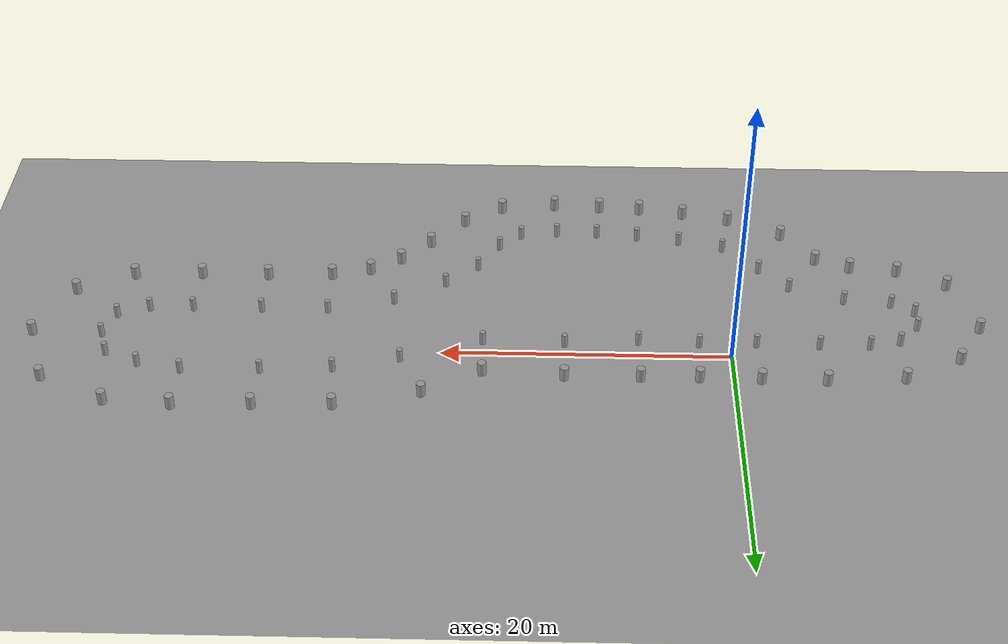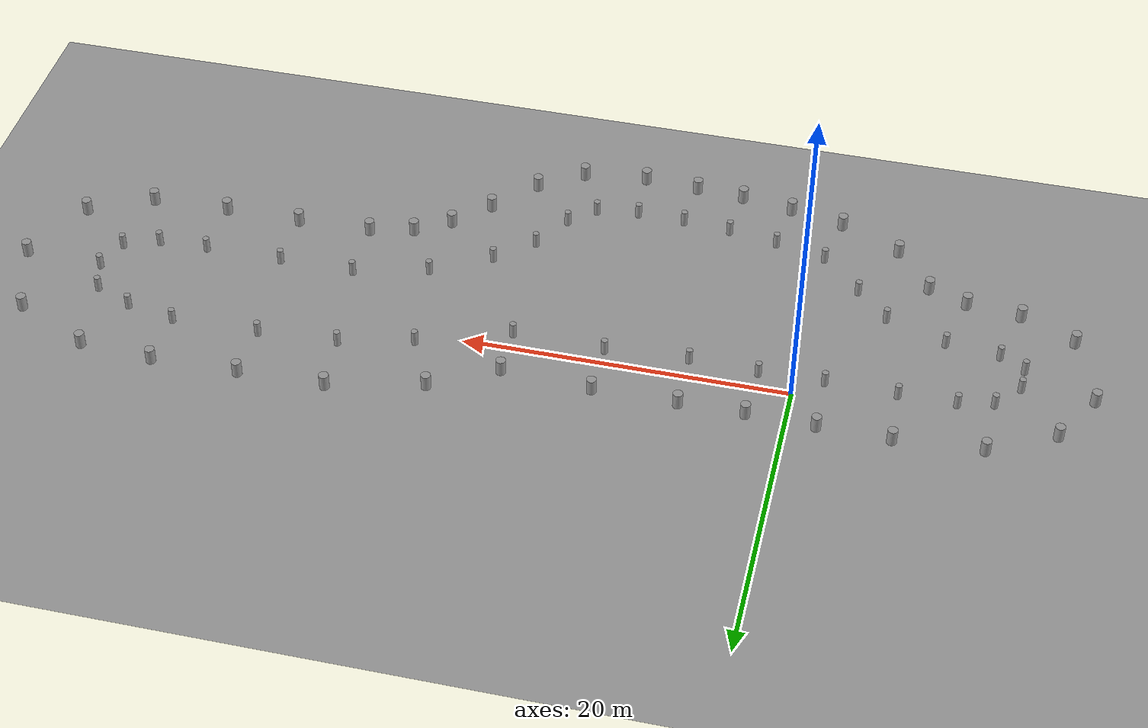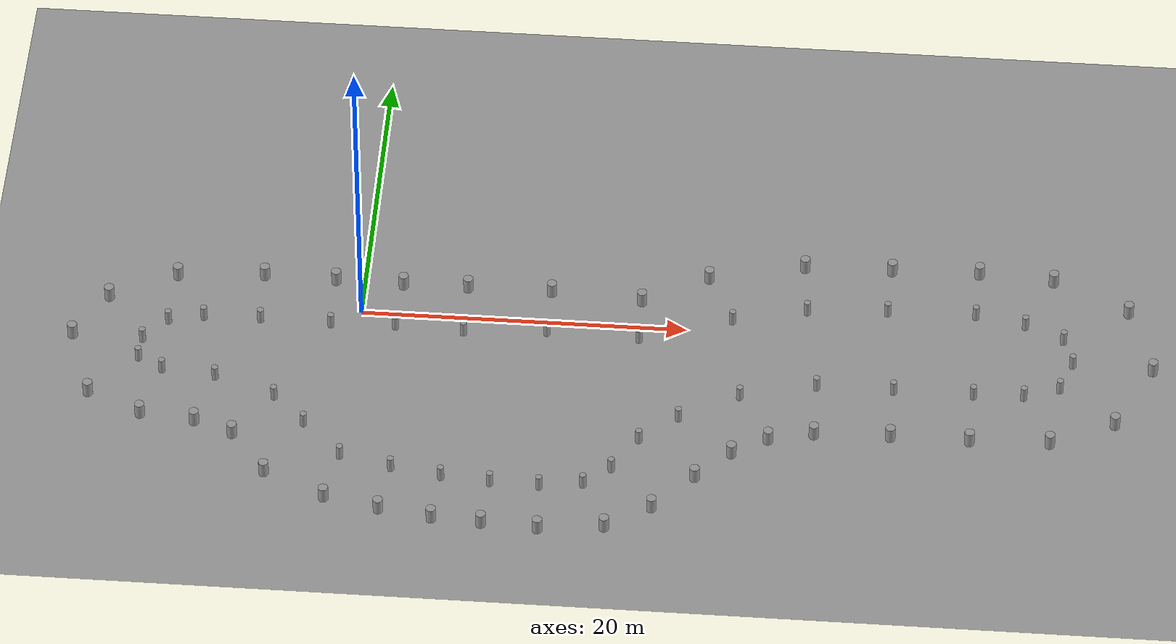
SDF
<sdf version="1.6">
 <world name="default">
  <light name="sun" type="directional">
   <pose>0 0 10 0 -0 0</pose>
   <diffuse>0.8 0.8 0.8 1</diffuse>
   <specular>0.2 0.2 0.2 1</specular>
   <attenuation>
    <range>1000</range>
    <constant>0.9</constant>
    <linear>0.01</linear>
    <quadratic>0.001</quadratic>
   </attenuation>
   <direction>0.5 0.1 -0.9</direction>
  </light>
  <scene><ambient>0.4 0.4 0.4 1</ambient><background>0.7 0.7 0.7 1</background><shadows>1</shadows></scene>
  <physics name="default_physics" default="0" type="ode">
   <max_step_size>0.01</max_step_size>
   <real_time_factor>1</real_time_factor>
   <real_time_update_rate>100</real_time_update_rate>
  </physics>
  <model name="ground_plane_0">
   <static>1</static>
   <link name="link">
    <collision name="collision">
     <geometry><plane><normal>0 0 1</normal><size>100 100</size></plane></geometry>
     <surface><friction><ode><mu>100</mu><mu2>50</mu2></ode></friction></surface>
    </collision>
    <visual name="visual">
     <cast_shadows>0</cast_shadows>
     <geometry><plane><normal>0 0 1</normal><size>100 100</size></plane></geometry>
     <material>
      <script><uri>file://media/materials/scripts/gazebo.material</uri><name>Gazebo/Grey</name></script>
     </material>
    </visual>
    <velocity_decay><linear>0</linear><angular>0</angular></velocity_decay>
   </link>
   <pose>0.497681 0 0 0 -0 0</pose>
  </model>
  <gravity>0 0 -9.8</gravity>
  <magnetic_field>6e-06 2.3e-05 -4.2e-05</magnetic_field>
  <atmosphere type="adiabatic"/>
  <spherical_coordinates>
   <surface_model>EARTH_WGS84</surface_model>
   <latitude_deg>0</latitude_deg>
   <longitude_deg>0</longitude_deg>
   <elevation>0</elevation>
   <heading_deg>0</heading_deg>
  </spherical_coordinates>
  <model name="cylinder_right_clone">
   <link name="link_0">
    <inertial>
     <mass>1</mass>
     <inertia><ixx>0.145833</ixx><ixy>0</ixy><ixz>0</ixz><iyy>0.145833</iyy><iyz>0</iyz><izz>0.125</izz></inertia>
    </inertial>
    <visual name="visual">
     <geometry><cylinder><radius>0.2</radius><length>1</length></cylinder></geometry>
     <material>
      <lighting>1</lighting>
      <script><uri>file://media/materials/scripts/gazebo.material</uri><name>Gazebo/Grey</name></script>
      <ambient>0.3 0.3 0.3 1</ambient>
      <diffuse>0.7 0.7 0.7 1</diffuse>
      <specular>0.01 0.01 0.01 1</specular>
      <emissive>0 0 0 1</emissive>
      <shader type="vertex"><normal_map>__default__</normal_map></shader>
     </material>
    </visual>
    <collision name="collision">
     <geometry><cylinder><radius>0.2</radius><length>1</length></cylinder></geometry>
     <surface>
      <friction>
       <ode><mu>1</mu><mu2>1</mu2><fdir1>0 0 0</fdir1><slip1>0</slip1><slip2>0</slip2></ode>
       <torsional>
        <coefficient>1</coefficient>
        <patch_radius>0</patch_radius>
        <surface_radius>0</surface_radius>
        <use_patch_radius>1</use_patch_radius>
        <ode><slip>0</slip></ode>
       </torsional>
      </friction>
      <bounce><restitution_coefficient>0</restitution_coefficient><threshold>1e+06</threshold></bounce>
      <contact>
       <collide_without_contact>0</collide_without_contact>
       <collide_without_contact_bitmask>1</collide_without_contact_bitmask>
       <collide_bitmask>1</collide_bitmask>
       <ode>
        <soft_cfm>0</soft_cfm>
        <soft_erp>0.2</soft_erp>
        <kp>1e+13</kp>
        <kd>1</kd>
        <max_vel>0.01</max_vel>
        <min_depth>0</min_depth>
       </ode>
       <bullet>
        <split_impulse>1</split_impulse>
        <split_impulse_penetration_threshold>-0.01</split_impulse_penetration_threshold>
        <soft_cfm>0</soft_cfm>
        <soft_erp>0.2</soft_erp>
        <kp>1e+13</kp>
        <kd>1</kd>
       </bullet>
      </contact>
     </surface>
    </collision>
   </link>
   <static>0</static>
   <pose>-1.75402 -1.29662 0.49912 0 -0 0.000422</pose>
  </model>
  <model name="cylinder_right_clone_0">
   <link name="link_0">
    <inertial>
     <mass>1</mass>
     <inertia><ixx>0.145833</ixx><ixy>0</ixy><ixz>0</ixz><iyy>0.145833</iyy><iyz>0</iyz><izz>0.125</izz></inertia>
    </inertial>
    <visual name="visual">
     <geometry><cylinder><radius>0.2</radius><length>1</length></cylinder></geometry>
     <material>
      <lighting>1</lighting>
      <script><uri>file://media/materials/scripts/gazebo.material</uri><name>Gazebo/Grey</name></script>
      <ambient>0.3 0.3 0.3 1</ambient>
      <diffuse>0.7 0.7 0.7 1</diffuse>
      <specular>0.01 0.01 0.01 1</specular>
      <emissive>0 0 0 1</emissive>
      <shader type="vertex"><normal_map>__default__</normal_map></shader>
     </material>
    </visual>
    <collision name="collision">
     <geometry><cylinder><radius>0.2</radius><length>1</length></cylinder></geometry>
     <surface>
      <friction>
       <ode><mu>1</mu><mu2>1</mu2><fdir1>0 0 0</fdir1><slip1>0</slip1><slip2>0</slip2></ode>
       <torsional>
        <coefficient>1</coefficient>
        <patch_radius>0</patch_radius>
        <surface_radius>0</surface_radius>
        <use_patch_radius>1</use_patch_radius>
        <ode><slip>0</slip></ode>
       </torsional>
      </friction>
      <bounce><restitution_coefficient>0</restitution_coefficient><threshold>1e+06</threshold></bounce>
      <contact>
       <collide_without_contact>0</collide_without_contact>
       <collide_without_contact_bitmask>1</collide_without_contact_bitmask>
       <collide_bitmask>1</collide_bitmask>
       <ode>
        <soft_cfm>0</soft_cfm>
        <soft_erp>0.2</soft_erp>
        <kp>1e+13</kp>
        <kd>1</kd>
        <max_vel>0.01</max_vel>
        <min_depth>0</min_depth>
       </ode>
       <bullet>
        <split_impulse>1</split_impulse>
        <split_impulse_penetration_threshold>-0.01</split_impulse_penetration_threshold>
        <soft_cfm>0</soft_cfm>
        <soft_erp>0.2</soft_erp>
        <kp>1e+13</kp>
        <kd>1</kd>
       </bullet>
      </contact>
     </surface>
    </collision>
   </link>
   <static>0</static>
   <pose>27.2508 1.99321 0.49912 0 -0 0.000407</pose>
  </model>
  <model name="cylinder_right_clone_2">
   <link name="link_0">
    <inertial>
     <mass>1</mass>
     <inertia><ixx>0.145833</ixx><ixy>0</ixy><ixz>0</ixz><iyy>0.145833</iyy><iyz>0</iyz><izz>0.125</izz></inertia>
    </inertial>
    <visual name="visual">
     <geometry><cylinder><radius>0.2</radius><length>1</length></cylinder></geometry>
     <material>
      <lighting>1</lighting>
      <script><uri>file://media/materials/scripts/gazebo.material</uri><name>Gazebo/Grey</name></script>
      <ambient>0.3 0.3 0.3 1</ambient>
      <diffuse>0.7 0.7 0.7 1</diffuse>
      <specular>0.01 0.01 0.01 1</specular>
      <emissive>0 0 0 1</emissive>
      <shader type="vertex"><normal_map>__default__</normal_map></shader>
     </material>
    </visual>
    <collision name="collision">
     <geometry><cylinder><radius>0.2</radius><length>1</length></cylinder></geometry>
     <surface>
      <friction>
       <ode><mu>1</mu><mu2>1</mu2><fdir1>0 0 0</fdir1><slip1>0</slip1><slip2>0</slip2></ode>
       <torsional>
        <coefficient>1</coefficient>
        <patch_radius>0</patch_radius>
        <surface_radius>0</surface_radius>
        <use_patch_radius>1</use_patch_radius>
        <ode><slip>0</slip></ode>
       </torsional>
      </friction>
      <bounce><restitution_coefficient>0</restitution_coefficient><threshold>1e+06</threshold></bounce>
      <contact>
       <collide_without_contact>0</collide_without_contact>
       <collide_without_contact_bitmask>1</collide_without_contact_bitmask>
       <collide_bitmask>1</collide_bitmask>
       <ode>
        <soft_cfm>0</soft_cfm>
        <soft_erp>0.2</soft_erp>
        <kp>1e+13</kp>
        <kd>1</kd>
        <max_vel>0.01</max_vel>
        <min_depth>0</min_depth>
       </ode>
       <bullet>
        <split_impulse>1</split_impulse>
        <split_impulse_penetration_threshold>-0.01</split_impulse_penetration_threshold>
        <soft_cfm>0</soft_cfm>
        <soft_erp>0.2</soft_erp>
        <kp>1e+13</kp>
        <kd>1</kd>
       </bullet>
      </contact>
     </surface>
    </collision>
   </link>
   <static>0</static>
   <pose>6.39184 -1.35941 0.49912 0 -0 0.000408</pose>
  </model>
  <model name="cylinder_right_clone_3">
   <link name="link_0">
    <inertial>
     <mass>1</mass>
     <inertia><ixx>0.145833</ixx><ixy>0</ixy><ixz>0</ixz><iyy>0.145833</iyy><iyz>0</iyz><izz>0.125</izz></inertia>
    </inertial>
    <visual name="visual">
     <geometry><cylinder><radius>0.2</radius><length>1</length></cylinder></geometry>
     <material>
      <lighting>1</lighting>
      <script><uri>file://media/materials/scripts/gazebo.material</uri><name>Gazebo/Grey</name></script>
      <ambient>0.3 0.3 0.3 1</ambient>
      <diffuse>0.7 0.7 0.7 1</diffuse>
      <specular>0.01 0.01 0.01 1</specular>
      <emissive>0 0 0 1</emissive>
      <shader type="vertex"><normal_map>__default__</normal_map></shader>
     </material>
    </visual>
    <collision name="collision">
     <geometry><cylinder><radius>0.2</radius><length>1</length></cylinder></geometry>
     <surface>
      <friction>
       <ode><mu>1</mu><mu2>1</mu2><fdir1>0 0 0</fdir1><slip1>0</slip1><slip2>0</slip2></ode>
       <torsional>
        <coefficient>1</coefficient>
        <patch_radius>0</patch_radius>
        <surface_radius>0</surface_radius>
        <use_patch_radius>1</use_patch_radius>
        <ode><slip>0</slip></ode>
       </torsional>
      </friction>
      <bounce><restitution_coefficient>0</restitution_coefficient><threshold>1e+06</threshold></bounce>
      <contact>
       <collide_without_contact>0</collide_without_contact>
       <collide_without_contact_bitmask>1</collide_without_contact_bitmask>
       <collide_bitmask>1</collide_bitmask>
       <ode>
        <soft_cfm>0</soft_cfm>
        <soft_erp>0.2</soft_erp>
        <kp>1e+13</kp>
        <kd>1</kd>
        <max_vel>0.01</max_vel>
        <min_depth>0</min_depth>
       </ode>
       <bullet>
        <split_impulse>1</split_impulse>
        <split_impulse_penetration_threshold>-0.01</split_impulse_penetration_threshold>
        <soft_cfm>0</soft_cfm>
        <soft_erp>0.2</soft_erp>
        <kp>1e+13</kp>
        <kd>1</kd>
       </bullet>
      </contact>
     </surface>
    </collision>
   </link>
   <static>0</static>
   <pose>17.1437 -1.15298 0.49912 0 -0 0.000408</pose>
  </model>
  <model name="cylinder_right_clone_5">
   <link name="link_0">
    <inertial>
     <mass>1</mass>
     <inertia><ixx>0.145833</ixx><ixy>0</ixy><ixz>0</ixz><iyy>0.145833</iyy><iyz>0</iyz><izz>0.125</izz></inertia>
    </inertial>
    <visual name="visual">
     <geometry><cylinder><radius>0.2</radius><length>1</length></cylinder></geometry>
     <material>
      <lighting>1</lighting>
      <script><uri>file://media/materials/scripts/gazebo.material</uri><name>Gazebo/Grey</name></script>
      <ambient>0.3 0.3 0.3 1</ambient>
      <diffuse>0.7 0.7 0.7 1</diffuse>
      <specular>0.01 0.01 0.01 1</specular>
      <emissive>0 0 0 1</emissive>
      <shader type="vertex"><normal_map>__default__</normal_map></shader>
     </material>
    </visual>
    <collision name="collision">
     <geometry><cylinder><radius>0.2</radius><length>1</length></cylinder></geometry>
     <surface>
      <friction>
       <ode><mu>1</mu><mu2>1</mu2><fdir1>0 0 0</fdir1><slip1>0</slip1><slip2>0</slip2></ode>
       <torsional>
        <coefficient>1</coefficient>
        <patch_radius>0</patch_radius>
        <surface_radius>0</surface_radius>
        <use_patch_radius>1</use_patch_radius>
        <ode><slip>0</slip></ode>
       </torsional>
      </friction>
      <bounce><restitution_coefficient>0</restitution_coefficient><threshold>1e+06</threshold></bounce>
      <contact>
       <collide_without_contact>0</collide_without_contact>
       <collide_without_contact_bitmask>1</collide_without_contact_bitmask>
       <collide_bitmask>1</collide_bitmask>
       <ode>
        <soft_cfm>0</soft_cfm>
        <soft_erp>0.2</soft_erp>
        <kp>1e+13</kp>
        <kd>1</kd>
        <max_vel>0.01</max_vel>
        <min_depth>0</min_depth>
       </ode>
       <bullet>
        <split_impulse>1</split_impulse>
        <split_impulse_penetration_threshold>-0.01</split_impulse_penetration_threshold>
        <soft_cfm>0</soft_cfm>
        <soft_erp>0.2</soft_erp>
        <kp>1e+13</kp>
        <kd>1</kd>
       </bullet>
      </contact>
     </surface>
    </collision>
   </link>
   <static>0</static>
   <pose>11.4796 -1.00544 0.49912 0 -0 0.000408</pose>
  </model>
  <model name="cylinder_left">
   <link name="link_1">
    <inertial>
     <mass>1</mass>
     <inertia><ixx>0.145833</ixx><ixy>0</ixy><ixz>0</ixz><iyy>0.145833</iyy><iyz>0</iyz><izz>0.125</izz></inertia>
    </inertial>
    <visual name="visual">
     <geometry><cylinder><radius>0.3</radius><length>1</length></cylinder></geometry>
     <material>
      <lighting>1</lighting>
      <script><uri>file://media/materials/scripts/gazebo.material</uri><name>Gazebo/Grey</name></script>
      <ambient>0.3 0.3 0.3 1</ambient>
      <diffuse>0.7 0.7 0.7 1</diffuse>
      <specular>0.01 0.01 0.01 1</specular>
      <emissive>0 0 0 1</emissive>
      <shader type="vertex"><normal_map>__default__</normal_map></shader>
     </material>
    </visual>
    <collision name="collision">
     <geometry><cylinder><radius>0.3</radius><length>1</length></cylinder></geometry>
     <surface>
      <friction>
       <ode><mu>1</mu><mu2>1</mu2><fdir1>0 0 0</fdir1><slip1>0</slip1><slip2>0</slip2></ode>
       <torsional>
        <coefficient>1</coefficient>
        <patch_radius>0</patch_radius>
        <surface_radius>0</surface_radius>
        <use_patch_radius>1</use_patch_radius>
        <ode><slip>0</slip></ode>
       </torsional>
      </friction>
      <bounce><restitution_coefficient>0</restitution_coefficient><threshold>1e+06</threshold></bounce>
      <contact>
       <collide_without_contact>0</collide_without_contact>
       <collide_without_contact_bitmask>1</collide_without_contact_bitmask>
       <collide_bitmask>1</collide_bitmask>
       <ode>
        <soft_cfm>0</soft_cfm>
        <soft_erp>0.2</soft_erp>
        <kp>1e+13</kp>
        <kd>1</kd>
        <max_vel>0.01</max_vel>
        <min_depth>0</min_depth>
       </ode>
       <bullet>
        <split_impulse>1</split_impulse>
        <split_impulse_penetration_threshold>-0.01</split_impulse_penetration_threshold>
        <soft_cfm>0</soft_cfm>
        <soft_erp>0.2</soft_erp>
        <kp>1e+13</kp>
        <kd>1</kd>
       </bullet>
      </contact>
     </surface>
    </collision>
   </link>
   <static>0</static>
   <pose>-1.80216 2.46852 0.49912 0 -0 0</pose>
  </model>
  <model name="cylinder_right_clone_6">
   <link name="link_0">
    <inertial>
     <mass>1</mass>
     <inertia><ixx>0.145833</ixx><ixy>0</ixy><ixz>0</ixz><iyy>0.145833</iyy><iyz>0</iyz><izz>0.125</izz></inertia>
    </inertial>
    <visual name="visual">
     <geometry><cylinder><radius>0.2</radius><length>1</length></cylinder></geometry>
     <material>
      <lighting>1</lighting>
      <script><uri>file://media/materials/scripts/gazebo.material</uri><name>Gazebo/Grey</name></script>
      <ambient>0.3 0.3 0.3 1</ambient>
      <diffuse>0.7 0.7 0.7 1</diffuse>
      <specular>0.01 0.01 0.01 1</specular>
      <emissive>0 0 0 1</emissive>
      <shader type="vertex"><normal_map>__default__</normal_map></shader>
     </material>
    </visual>
    <collision name="collision">
     <geometry><cylinder><radius>0.2</radius><length>1</length></cylinder></geometry>
     <surface>
      <friction>
       <ode><mu>1</mu><mu2>1</mu2><fdir1>0 0 0</fdir1><slip1>0</slip1><slip2>0</slip2></ode>
       <torsional>
        <coefficient>1</coefficient>
        <patch_radius>0</patch_radius>
        <surface_radius>0</surface_radius>
        <use_patch_radius>1</use_patch_radius>
        <ode><slip>0</slip></ode>
       </torsional>
      </friction>
      <bounce><restitution_coefficient>0</restitution_coefficient><threshold>1e+06</threshold></bounce>
      <contact>
       <collide_without_contact>0</collide_without_contact>
       <collide_without_contact_bitmask>1</collide_without_contact_bitmask>
       <collide_bitmask>1</collide_bitmask>
       <ode>
        <soft_cfm>0</soft_cfm>
        <soft_erp>0.2</soft_erp>
        <kp>1e+13</kp>
        <kd>1</kd>
        <max_vel>0.01</max_vel>
        <min_depth>0</min_depth>
       </ode>
       <bullet>
        <split_impulse>1</split_impulse>
        <split_impulse_penetration_threshold>-0.01</split_impulse_penetration_threshold>
        <soft_cfm>0</soft_cfm>
        <soft_erp>0.2</soft_erp>
        <kp>1e+13</kp>
        <kd>1</kd>
       </bullet>
      </contact>
     </surface>
    </collision>
   </link>
   <static>0</static>
   <pose>22.7344 0.858613 0.49912 0 -0 0.000422</pose>
  </model>
  <model name="cylinder_left_clone">
   <link name="link_1">
    <inertial>
     <mass>1</mass>
     <inertia><ixx>0.145833</ixx><ixy>0</ixy><ixz>0</ixz><iyy>0.145833</iyy><iyz>0</iyz><izz>0.125</izz></inertia>
    </inertial>
    <visual name="visual">
     <geometry><cylinder><radius>0.3</radius><length>1</length></cylinder></geometry>
     <material>
      <lighting>1</lighting>
      <script><uri>file://media/materials/scripts/gazebo.material</uri><name>Gazebo/Grey</name></script>
      <ambient>0.3 0.3 0.3 1</ambient>
      <diffuse>0.7 0.7 0.7 1</diffuse>
      <specular>0.01 0.01 0.01 1</specular>
      <emissive>0 0 0 1</emissive>
      <shader type="vertex"><normal_map>__default__</normal_map></shader>
     </material>
    </visual>
    <collision name="collision">
     <geometry><cylinder><radius>0.3</radius><length>1</length></cylinder></geometry>
     <surface>
      <friction>
       <ode><mu>1</mu><mu2>1</mu2><fdir1>0 0 0</fdir1><slip1>0</slip1><slip2>0</slip2></ode>
       <torsional>
        <coefficient>1</coefficient>
        <patch_radius>0</patch_radius>
        <surface_radius>0</surface_radius>
        <use_patch_radius>1</use_patch_radius>
        <ode><slip>0</slip></ode>
       </torsional>
      </friction>
      <bounce><restitution_coefficient>0</restitution_coefficient><threshold>1e+06</threshold></bounce>
      <contact>
       <collide_without_contact>0</collide_without_contact>
       <collide_without_contact_bitmask>1</collide_without_contact_bitmask>
       <collide_bitmask>1</collide_bitmask>
       <ode>
        <soft_cfm>0</soft_cfm>
        <soft_erp>0.2</soft_erp>
        <kp>1e+13</kp>
        <kd>1</kd>
        <max_vel>0.01</max_vel>
        <min_depth>0</min_depth>
       </ode>
       <bullet>
        <split_impulse>1</split_impulse>
        <split_impulse_penetration_threshold>-0.01</split_impulse_penetration_threshold>
        <soft_cfm>0</soft_cfm>
        <soft_erp>0.2</soft_erp>
        <kp>1e+13</kp>
        <kd>1</kd>
       </bullet>
      </contact>
     </surface>
    </collision>
   </link>
   <static>0</static>
   <pose>2.36241 2.40356 0.49912 0 -0 0</pose>
  </model>
  <model name="cylinder_left_clone_1">
   <link name="link_1">
    <inertial>
     <mass>1</mass>
     <inertia><ixx>0.145833</ixx><ixy>0</ixy><ixz>0</ixz><iyy>0.145833</iyy><iyz>0</iyz><izz>0.125</izz></inertia>
    </inertial>
    <visual name="visual">
     <geometry><cylinder><radius>0.3</radius><length>1</length></cylinder></geometry>
     <material>
      <lighting>1</lighting>
      <script><uri>file://media/materials/scripts/gazebo.material</uri><name>Gazebo/Grey</name></script>
      <ambient>0.3 0.3 0.3 1</ambient>
      <diffuse>0.7 0.7 0.7 1</diffuse>
      <specular>0.01 0.01 0.01 1</specular>
      <emissive>0 0 0 1</emissive>
      <shader type="vertex"><normal_map>__default__</normal_map></shader>
     </material>
    </visual>
    <collision name="collision">
     <geometry><cylinder><radius>0.3</radius><length>1</length></cylinder></geometry>
     <surface>
      <friction>
       <ode><mu>1</mu><mu2>1</mu2><fdir1>0 0 0</fdir1><slip1>0</slip1><slip2>0</slip2></ode>
       <torsional>
        <coefficient>1</coefficient>
        <patch_radius>0</patch_radius>
        <surface_radius>0</surface_radius>
        <use_patch_radius>1</use_patch_radius>
        <ode><slip>0</slip></ode>
       </torsional>
      </friction>
      <bounce><restitution_coefficient>0</restitution_coefficient><threshold>1e+06</threshold></bounce>
      <contact>
       <collide_without_contact>0</collide_without_contact>
       <collide_without_contact_bitmask>1</collide_without_contact_bitmask>
       <collide_bitmask>1</collide_bitmask>
       <ode>
        <soft_cfm>0</soft_cfm>
        <soft_erp>0.2</soft_erp>
        <kp>1e+13</kp>
        <kd>1</kd>
        <max_vel>0.01</max_vel>
        <min_depth>0</min_depth>
       </ode>
       <bullet>
        <split_impulse>1</split_impulse>
        <split_impulse_penetration_threshold>-0.01</split_impulse_penetration_threshold>
        <soft_cfm>0</soft_cfm>
        <soft_erp>0.2</soft_erp>
        <kp>1e+13</kp>
        <kd>1</kd>
       </bullet>
      </contact>
     </surface>
    </collision>
   </link>
   <static>0</static>
   <pose>6.35243 2.44454 0.49912 0 -0 0</pose>
  </model>
  <model name="cylinder_left_clone_2">
   <link name="link_1">
    <inertial>
     <mass>1</mass>
     <inertia><ixx>0.145833</ixx><ixy>0</ixy><ixz>0</ixz><iyy>0.145833</iyy><iyz>0</iyz><izz>0.125</izz></inertia>
    </inertial>
    <visual name="visual">
     <geometry><cylinder><radius>0.3</radius><length>1</length></cylinder></geometry>
     <material>
      <lighting>1</lighting>
      <script><uri>file://media/materials/scripts/gazebo.material</uri><name>Gazebo/Grey</name></script>
      <ambient>0.3 0.3 0.3 1</ambient>
      <diffuse>0.7 0.7 0.7 1</diffuse>
      <specular>0.01 0.01 0.01 1</specular>
      <emissive>0 0 0 1</emissive>
      <shader type="vertex"><normal_map>__default__</normal_map></shader>
     </material>
    </visual>
    <collision name="collision">
     <geometry><cylinder><radius>0.3</radius><length>1</length></cylinder></geometry>
     <surface>
      <friction>
       <ode><mu>1</mu><mu2>1</mu2><fdir1>0 0 0</fdir1><slip1>0</slip1><slip2>0</slip2></ode>
       <torsional>
        <coefficient>1</coefficient>
        <patch_radius>0</patch_radius>
        <surface_radius>0</surface_radius>
        <use_patch_radius>1</use_patch_radius>
        <ode><slip>0</slip></ode>
       </torsional>
      </friction>
      <bounce><restitution_coefficient>0</restitution_coefficient><threshold>1e+06</threshold></bounce>
      <contact>
       <collide_without_contact>0</collide_without_contact>
       <collide_without_contact_bitmask>1</collide_without_contact_bitmask>
       <collide_bitmask>1</collide_bitmask>
       <ode>
        <soft_cfm>0</soft_cfm>
        <soft_erp>0.2</soft_erp>
        <kp>1e+13</kp>
        <kd>1</kd>
        <max_vel>0.01</max_vel>
        <min_depth>0</min_depth>
       </ode>
       <bullet>
        <split_impulse>1</split_impulse>
        <split_impulse_penetration_threshold>-0.01</split_impulse_penetration_threshold>
        <soft_cfm>0</soft_cfm>
        <soft_erp>0.2</soft_erp>
        <kp>1e+13</kp>
        <kd>1</kd>
       </bullet>
      </contact>
     </surface>
    </collision>
   </link>
   <static>0</static>
   <pose>32.2673 5.86285 0.49912 0 -0 0</pose>
  </model>
  <model name="cylinder_right_clone_7">
   <link name="link_0">
    <inertial>
     <mass>1</mass>
     <inertia><ixx>0.145833</ixx><ixy>0</ixy><ixz>0</ixz><iyy>0.145833</iyy><iyz>0</iyz><izz>0.125</izz></inertia>
    </inertial>
    <visual name="visual">
     <geometry><cylinder><radius>0.2</radius><length>1</length></cylinder></geometry>
     <material>
      <lighting>1</lighting>
      <script><uri>file://media/materials/scripts/gazebo.material</uri><name>Gazebo/Grey</name></script>
      <ambient>0.3 0.3 0.3 1</ambient>
      <diffuse>0.7 0.7 0.7 1</diffuse>
      <specular>0.01 0.01 0.01 1</specular>
      <emissive>0 0 0 1</emissive>
      <shader type="vertex"><normal_map>__default__</normal_map></shader>
     </material>
    </visual>
    <collision name="collision">
     <geometry><cylinder><radius>0.2</radius><length>1</length></cylinder></geometry>
     <surface>
      <friction>
       <ode><mu>1</mu><mu2>1</mu2><fdir1>0 0 0</fdir1><slip1>0</slip1><slip2>0</slip2></ode>
       <torsional>
        <coefficient>1</coefficient>
        <patch_radius>0</patch_radius>
        <surface_radius>0</surface_radius>
        <use_patch_radius>1</use_patch_radius>
        <ode><slip>0</slip></ode>
       </torsional>
      </friction>
      <bounce><restitution_coefficient>0</restitution_coefficient><threshold>1e+06</threshold></bounce>
      <contact>
       <collide_without_contact>0</collide_without_contact>
       <collide_without_contact_bitmask>1</collide_without_contact_bitmask>
       <collide_bitmask>1</collide_bitmask>
       <ode>
        <soft_cfm>0</soft_cfm>
        <soft_erp>0.2</soft_erp>
        <kp>1e+13</kp>
        <kd>1</kd>
        <max_vel>0.01</max_vel>
        <min_depth>0</min_depth>
       </ode>
       <bullet>
        <split_impulse>1</split_impulse>
        <split_impulse_penetration_threshold>-0.01</split_impulse_penetration_threshold>
        <soft_cfm>0</soft_cfm>
        <soft_erp>0.2</soft_erp>
        <kp>1e+13</kp>
        <kd>1</kd>
       </bullet>
      </contact>
     </surface>
    </collision>
   </link>
   <static>0</static>
   <pose>37.57 2.39361 0.49912 0 -0 0.000406</pose>
  </model>
  <model name="cylinder_right_clone_10">
   <link name="link_0">
    <inertial>
     <mass>1</mass>
     <inertia><ixx>0.145833</ixx><ixy>0</ixy><ixz>0</ixz><iyy>0.145833</iyy><iyz>0</iyz><izz>0.125</izz></inertia>
    </inertial>
    <visual name="visual">
     <geometry><cylinder><radius>0.2</radius><length>1</length></cylinder></geometry>
     <material>
      <lighting>1</lighting>
      <script><uri>file://media/materials/scripts/gazebo.material</uri><name>Gazebo/Grey</name></script>
      <ambient>0.3 0.3 0.3 1</ambient>
      <diffuse>0.7 0.7 0.7 1</diffuse>
      <specular>0.01 0.01 0.01 1</specular>
      <emissive>0 0 0 1</emissive>
      <shader type="vertex"><normal_map>__default__</normal_map></shader>
     </material>
    </visual>
    <collision name="collision">
     <geometry><cylinder><radius>0.2</radius><length>1</length></cylinder></geometry>
     <surface>
      <friction>
       <ode><mu>1</mu><mu2>1</mu2><fdir1>0 0 0</fdir1><slip1>0</slip1><slip2>0</slip2></ode>
       <torsional>
        <coefficient>1</coefficient>
        <patch_radius>0</patch_radius>
        <surface_radius>0</surface_radius>
        <use_patch_radius>1</use_patch_radius>
        <ode><slip>0</slip></ode>
       </torsional>
      </friction>
      <bounce><restitution_coefficient>0</restitution_coefficient><threshold>1e+06</threshold></bounce>
      <contact>
       <collide_without_contact>0</collide_without_contact>
       <collide_without_contact_bitmask>1</collide_without_contact_bitmask>
       <collide_bitmask>1</collide_bitmask>
       <ode>
        <soft_cfm>0</soft_cfm>
        <soft_erp>0.2</soft_erp>
        <kp>1e+13</kp>
        <kd>1</kd>
        <max_vel>0.01</max_vel>
        <min_depth>0</min_depth>
       </ode>
       <bullet>
        <split_impulse>1</split_impulse>
        <split_impulse_penetration_threshold>-0.01</split_impulse_penetration_threshold>
        <soft_cfm>0</soft_cfm>
        <soft_erp>0.2</soft_erp>
        <kp>1e+13</kp>
        <kd>1</kd>
       </bullet>
      </contact>
     </surface>
    </collision>
   </link>
   <static>0</static>
   <pose>2.19522 -1.17916 0.49912 0 -0 0.000408</pose>
  </model>
  <model name="cylinder_right_clone_11">
   <link name="link_0">
    <inertial>
     <mass>1</mass>
     <inertia><ixx>0.145833</ixx><ixy>0</ixy><ixz>0</ixz><iyy>0.145833</iyy><iyz>0</iyz><izz>0.125</izz></inertia>
    </inertial>
    <visual name="visual">
     <geometry><cylinder><radius>0.2</radius><length>1</length></cylinder></geometry>
     <material>
      <lighting>1</lighting>
      <script><uri>file://media/materials/scripts/gazebo.material</uri><name>Gazebo/Grey</name></script>
      <ambient>0.3 0.3 0.3 1</ambient>
      <diffuse>0.7 0.7 0.7 1</diffuse>
      <specular>0.01 0.01 0.01 1</specular>
      <emissive>0 0 0 1</emissive>
      <shader type="vertex"><normal_map>__default__</normal_map></shader>
     </material>
    </visual>
    <collision name="collision">
     <geometry><cylinder><radius>0.2</radius><length>1</length></cylinder></geometry>
     <surface>
      <friction>
       <ode><mu>1</mu><mu2>1</mu2><fdir1>0 0 0</fdir1><slip1>0</slip1><slip2>0</slip2></ode>
       <torsional>
        <coefficient>1</coefficient>
        <patch_radius>0</patch_radius>
        <surface_radius>0</surface_radius>
        <use_patch_radius>1</use_patch_radius>
        <ode><slip>0</slip></ode>
       </torsional>
      </friction>
      <bounce><restitution_coefficient>0</restitution_coefficient><threshold>1e+06</threshold></bounce>
      <contact>
       <collide_without_contact>0</collide_without_contact>
       <collide_without_contact_bitmask>1</collide_without_contact_bitmask>
       <collide_bitmask>1</collide_bitmask>
       <ode>
        <soft_cfm>0</soft_cfm>
        <soft_erp>0.2</soft_erp>
        <kp>1e+13</kp>
        <kd>1</kd>
        <max_vel>0.01</max_vel>
        <min_depth>0</min_depth>
       </ode>
       <bullet>
        <split_impulse>1</split_impulse>
        <split_impulse_penetration_threshold>-0.01</split_impulse_penetration_threshold>
        <soft_cfm>0</soft_cfm>
        <soft_erp>0.2</soft_erp>
        <kp>1e+13</kp>
        <kd>1</kd>
       </bullet>
      </contact>
     </surface>
    </collision>
   </link>
   <static>0</static>
   <pose>32.1657 2.28849 0.49912 0 -0 0.000408</pose>
  </model>
  <model name="cylinder_left_clone_2_clone">
   <link name="link_1">
    <inertial>
     <mass>1</mass>
     <inertia><ixx>0.145833</ixx><ixy>0</ixy><ixz>0</ixz><iyy>0.145833</iyy><iyz>0</iyz><izz>0.125</izz></inertia>
    </inertial>
    <visual name="visual">
     <geometry><cylinder><radius>0.3</radius><length>1</length></cylinder></geometry>
     <material>
      <lighting>1</lighting>
      <script><uri>file://media/materials/scripts/gazebo.material</uri><name>Gazebo/Grey</name></script>
      <ambient>0.3 0.3 0.3 1</ambient>
      <diffuse>0.7 0.7 0.7 1</diffuse>
      <specular>0.01 0.01 0.01 1</specular>
      <emissive>0 0 0 1</emissive>
      <shader type="vertex"><normal_map>__default__</normal_map></shader>
     </material>
    </visual>
    <collision name="collision">
     <geometry><cylinder><radius>0.3</radius><length>1</length></cylinder></geometry>
     <surface>
      <friction>
       <ode><mu>1</mu><mu2>1</mu2><fdir1>0 0 0</fdir1><slip1>0</slip1><slip2>0</slip2></ode>
       <torsional>
        <coefficient>1</coefficient>
        <patch_radius>0</patch_radius>
        <surface_radius>0</surface_radius>
        <use_patch_radius>1</use_patch_radius>
        <ode><slip>0</slip></ode>
       </torsional>
      </friction>
      <bounce><restitution_coefficient>0</restitution_coefficient><threshold>1e+06</threshold></bounce>
      <contact>
       <collide_without_contact>0</collide_without_contact>
       <collide_without_contact_bitmask>1</collide_without_contact_bitmask>
       <collide_bitmask>1</collide_bitmask>
       <ode>
        <soft_cfm>0</soft_cfm>
        <soft_erp>0.2</soft_erp>
        <kp>1e+13</kp>
        <kd>1</kd>
        <max_vel>0.01</max_vel>
        <min_depth>0</min_depth>
       </ode>
       <bullet>
        <split_impulse>1</split_impulse>
        <split_impulse_penetration_threshold>-0.01</split_impulse_penetration_threshold>
        <soft_cfm>0</soft_cfm>
        <soft_erp>0.2</soft_erp>
        <kp>1e+13</kp>
        <kd>1</kd>
       </bullet>
      </contact>
     </surface>
    </collision>
   </link>
   <static>0</static>
   <pose>21.0723 4.35557 0.49912 0 0 -2.56426</pose>
  </model>
  <model name="cylinder_left_clone_2_clone_clone">
   <link name="link_1">
    <inertial>
     <mass>1</mass>
     <inertia><ixx>0.145833</ixx><ixy>0</ixy><ixz>0</ixz><iyy>0.145833</iyy><iyz>0</iyz><izz>0.125</izz></inertia>
    </inertial>
    <visual name="visual">
     <geometry><cylinder><radius>0.3</radius><length>1</length></cylinder></geometry>
     <material>
      <lighting>1</lighting>
      <script><uri>file://media/materials/scripts/gazebo.material</uri><name>Gazebo/Grey</name></script>
      <ambient>0.3 0.3 0.3 1</ambient>
      <diffuse>0.7 0.7 0.7 1</diffuse>
      <specular>0.01 0.01 0.01 1</specular>
      <emissive>0 0 0 1</emissive>
      <shader type="vertex"><normal_map>__default__</normal_map></shader>
     </material>
    </visual>
    <collision name="collision">
     <geometry><cylinder><radius>0.3</radius><length>1</length></cylinder></geometry>
     <surface>
      <friction>
       <ode><mu>1</mu><mu2>1</mu2><fdir1>0 0 0</fdir1><slip1>0</slip1><slip2>0</slip2></ode>
       <torsional>
        <coefficient>1</coefficient>
        <patch_radius>0</patch_radius>
        <surface_radius>0</surface_radius>
        <use_patch_radius>1</use_patch_radius>
        <ode><slip>0</slip></ode>
       </torsional>
      </friction>
      <bounce><restitution_coefficient>0</restitution_coefficient><threshold>1e+06</threshold></bounce>
      <contact>
       <collide_without_contact>0</collide_without_contact>
       <collide_without_contact_bitmask>1</collide_without_contact_bitmask>
       <collide_bitmask>1</collide_bitmask>
       <ode>
        <soft_cfm>0</soft_cfm>
        <soft_erp>0.2</soft_erp>
        <kp>1e+13</kp>
        <kd>1</kd>
        <max_vel>0.01</max_vel>
        <min_depth>0</min_depth>
       </ode>
       <bullet>
        <split_impulse>1</split_impulse>
        <split_impulse_penetration_threshold>-0.01</split_impulse_penetration_threshold>
        <soft_cfm>0</soft_cfm>
        <soft_erp>0.2</soft_erp>
        <kp>1e+13</kp>
        <kd>1</kd>
       </bullet>
      </contact>
     </surface>
    </collision>
   </link>
   <static>0</static>
   <pose>17.0861 2.10228 0.49912 0 -0 0</pose>
  </model>
  <model name="cylinder_left_clone_2_clone_clone_0">
   <link name="link_1">
    <inertial>
     <mass>1</mass>
     <inertia><ixx>0.145833</ixx><ixy>0</ixy><ixz>0</ixz><iyy>0.145833</iyy><iyz>0</iyz><izz>0.125</izz></inertia>
    </inertial>
    <visual name="visual">
     <geometry><cylinder><radius>0.3</radius><length>1</length></cylinder></geometry>
     <material>
      <lighting>1</lighting>
      <script><uri>file://media/materials/scripts/gazebo.material</uri><name>Gazebo/Grey</name></script>
      <ambient>0.3 0.3 0.3 1</ambient>
      <diffuse>0.7 0.7 0.7 1</diffuse>
      <specular>0.01 0.01 0.01 1</specular>
      <emissive>0 0 0 1</emissive>
      <shader type="vertex"><normal_map>__default__</normal_map></shader>
     </material>
    </visual>
    <collision name="collision">
     <geometry><cylinder><radius>0.3</radius><length>1</length></cylinder></geometry>
     <surface>
      <friction>
       <ode><mu>1</mu><mu2>1</mu2><fdir1>0 0 0</fdir1><slip1>0</slip1><slip2>0</slip2></ode>
       <torsional>
        <coefficient>1</coefficient>
        <patch_radius>0</patch_radius>
        <surface_radius>0</surface_radius>
        <use_patch_radius>1</use_patch_radius>
        <ode><slip>0</slip></ode>
       </torsional>
      </friction>
      <bounce><restitution_coefficient>0</restitution_coefficient><threshold>1e+06</threshold></bounce>
      <contact>
       <collide_without_contact>0</collide_without_contact>
       <collide_without_contact_bitmask>1</collide_without_contact_bitmask>
       <collide_bitmask>1</collide_bitmask>
       <ode>
        <soft_cfm>0</soft_cfm>
        <soft_erp>0.2</soft_erp>
        <kp>1e+13</kp>
        <kd>1</kd>
        <max_vel>0.01</max_vel>
        <min_depth>0</min_depth>
       </ode>
       <bullet>
        <split_impulse>1</split_impulse>
        <split_impulse_penetration_threshold>-0.01</split_impulse_penetration_threshold>
        <soft_cfm>0</soft_cfm>
        <soft_erp>0.2</soft_erp>
        <kp>1e+13</kp>
        <kd>1</kd>
       </bullet>
      </contact>
     </surface>
    </collision>
   </link>
   <static>0</static>
   <pose>26.9015 5.74729 0.49912 0 -0 0</pose>
  </model>
  <model name="cylinder_left_clone_2_clone_0">
   <link name="link_1">
    <inertial>
     <mass>1</mass>
     <inertia><ixx>0.145833</ixx><ixy>0</ixy><ixz>0</ixz><iyy>0.145833</iyy><iyz>0</iyz><izz>0.125</izz></inertia>
    </inertial>
    <visual name="visual">
     <geometry><cylinder><radius>0.3</radius><length>1</length></cylinder></geometry>
     <material>
      <lighting>1</lighting>
      <script><uri>file://media/materials/scripts/gazebo.material</uri><name>Gazebo/Grey</name></script>
      <ambient>0.3 0.3 0.3 1</ambient>
      <diffuse>0.7 0.7 0.7 1</diffuse>
      <specular>0.01 0.01 0.01 1</specular>
      <emissive>0 0 0 1</emissive>
      <shader type="vertex"><normal_map>__default__</normal_map></shader>
     </material>
    </visual>
    <collision name="collision">
     <geometry><cylinder><radius>0.3</radius><length>1</length></cylinder></geometry>
     <surface>
      <friction>
       <ode><mu>1</mu><mu2>1</mu2><fdir1>0 0 0</fdir1><slip1>0</slip1><slip2>0</slip2></ode>
       <torsional>
        <coefficient>1</coefficient>
        <patch_radius>0</patch_radius>
        <surface_radius>0</surface_radius>
        <use_patch_radius>1</use_patch_radius>
        <ode><slip>0</slip></ode>
       </torsional>
      </friction>
      <bounce><restitution_coefficient>0</restitution_coefficient><threshold>1e+06</threshold></bounce>
      <contact>
       <collide_without_contact>0</collide_without_contact>
       <collide_without_contact_bitmask>1</collide_without_contact_bitmask>
       <collide_bitmask>1</collide_bitmask>
       <ode>
        <soft_cfm>0</soft_cfm>
        <soft_erp>0.2</soft_erp>
        <kp>1e+13</kp>
        <kd>1</kd>
        <max_vel>0.01</max_vel>
        <min_depth>0</min_depth>
       </ode>
       <bullet>
        <split_impulse>1</split_impulse>
        <split_impulse_penetration_threshold>-0.01</split_impulse_penetration_threshold>
        <soft_cfm>0</soft_cfm>
        <soft_erp>0.2</soft_erp>
        <kp>1e+13</kp>
        <kd>1</kd>
       </bullet>
      </contact>
     </surface>
    </collision>
   </link>
   <static>0</static>
   <pose>37.6347 5.98755 0.49912 0 -0 0</pose>
  </model>
  <model name="cylinder_left_clone_2_clone_1">
   <link name="link_1">
    <inertial>
     <mass>1</mass>
     <inertia><ixx>0.145833</ixx><ixy>0</ixy><ixz>0</ixz><iyy>0.145833</iyy><iyz>0</iyz><izz>0.125</izz></inertia>
    </inertial>
    <visual name="visual">
     <geometry><cylinder><radius>0.3</radius><length>1</length></cylinder></geometry>
     <material>
      <lighting>1</lighting>
      <script><uri>file://media/materials/scripts/gazebo.material</uri><name>Gazebo/Grey</name></script>
      <ambient>0.3 0.3 0.3 1</ambient>
      <diffuse>0.7 0.7 0.7 1</diffuse>
      <specular>0.01 0.01 0.01 1</specular>
      <emissive>0 0 0 1</emissive>
      <shader type="vertex"><normal_map>__default__</normal_map></shader>
     </material>
    </visual>
    <collision name="collision">
     <geometry><cylinder><radius>0.3</radius><length>1</length></cylinder></geometry>
     <surface>
      <friction>
       <ode><mu>1</mu><mu2>1</mu2><fdir1>0 0 0</fdir1><slip1>0</slip1><slip2>0</slip2></ode>
       <torsional>
        <coefficient>1</coefficient>
        <patch_radius>0</patch_radius>
        <surface_radius>0</surface_radius>
        <use_patch_radius>1</use_patch_radius>
        <ode><slip>0</slip></ode>
       </torsional>
      </friction>
      <bounce><restitution_coefficient>0</restitution_coefficient><threshold>1e+06</threshold></bounce>
      <contact>
       <collide_without_contact>0</collide_without_contact>
       <collide_without_contact_bitmask>1</collide_without_contact_bitmask>
       <collide_bitmask>1</collide_bitmask>
       <ode>
        <soft_cfm>0</soft_cfm>
        <soft_erp>0.2</soft_erp>
        <kp>1e+13</kp>
        <kd>1</kd>
        <max_vel>0.01</max_vel>
        <min_depth>0</min_depth>
       </ode>
       <bullet>
        <split_impulse>1</split_impulse>
        <split_impulse_penetration_threshold>-0.01</split_impulse_penetration_threshold>
        <soft_cfm>0</soft_cfm>
        <soft_erp>0.2</soft_erp>
        <kp>1e+13</kp>
        <kd>1</kd>
       </bullet>
      </contact>
     </surface>
    </collision>
   </link>
   <static>0</static>
   <pose>46.8917 3.34862 0.49912 0 -0 0</pose>
  </model>
  <model name="cylinder_left_clone_2_clone_2">
   <link name="link_1">
    <inertial>
     <mass>1</mass>
     <inertia><ixx>0.145833</ixx><ixy>0</ixy><ixz>0</ixz><iyy>0.145833</iyy><iyz>0</iyz><izz>0.125</izz></inertia>
    </inertial>
    <visual name="visual">
     <geometry><cylinder><radius>0.3</radius><length>1</length></cylinder></geometry>
     <material>
      <lighting>1</lighting>
      <script><uri>file://media/materials/scripts/gazebo.material</uri><name>Gazebo/Grey</name></script>
      <ambient>0.3 0.3 0.3 1</ambient>
      <diffuse>0.7 0.7 0.7 1</diffuse>
      <specular>0.01 0.01 0.01 1</specular>
      <emissive>0 0 0 1</emissive>
      <shader type="vertex"><normal_map>__default__</normal_map></shader>
     </material>
    </visual>
    <collision name="collision">
     <geometry><cylinder><radius>0.3</radius><length>1</length></cylinder></geometry>
     <surface>
      <friction>
       <ode><mu>1</mu><mu2>1</mu2><fdir1>0 0 0</fdir1><slip1>0</slip1><slip2>0</slip2></ode>
       <torsional>
        <coefficient>1</coefficient>
        <patch_radius>0</patch_radius>
        <surface_radius>0</surface_radius>
        <use_patch_radius>1</use_patch_radius>
        <ode><slip>0</slip></ode>
       </torsional>
      </friction>
      <bounce><restitution_coefficient>0</restitution_coefficient><threshold>1e+06</threshold></bounce>
      <contact>
       <collide_without_contact>0</collide_without_contact>
       <collide_without_contact_bitmask>1</collide_without_contact_bitmask>
       <collide_bitmask>1</collide_bitmask>
       <ode>
        <soft_cfm>0</soft_cfm>
        <soft_erp>0.2</soft_erp>
        <kp>1e+13</kp>
        <kd>1</kd>
        <max_vel>0.01</max_vel>
        <min_depth>0</min_depth>
       </ode>
       <bullet>
        <split_impulse>1</split_impulse>
        <split_impulse_penetration_threshold>-0.01</split_impulse_penetration_threshold>
        <soft_cfm>0</soft_cfm>
        <soft_erp>0.2</soft_erp>
        <kp>1e+13</kp>
        <kd>1</kd>
       </bullet>
      </contact>
     </surface>
    </collision>
   </link>
   <static>0</static>
   <pose>48.5115 -1.47382 0.49912 0 -0 0</pose>
  </model>
  <model name="cylinder_left_clone_2_clone_3">
   <link name="link_1">
    <inertial>
     <mass>1</mass>
     <inertia><ixx>0.145833</ixx><ixy>0</ixy><ixz>0</ixz><iyy>0.145833</iyy><iyz>0</iyz><izz>0.125</izz></inertia>
    </inertial>
    <visual name="visual">
     <geometry><cylinder><radius>0.3</radius><length>1</length></cylinder></geometry>
     <material>
      <lighting>1</lighting>
      <script><uri>file://media/materials/scripts/gazebo.material</uri><name>Gazebo/Grey</name></script>
      <ambient>0.3 0.3 0.3 1</ambient>
      <diffuse>0.7 0.7 0.7 1</diffuse>
      <specular>0.01 0.01 0.01 1</specular>
      <emissive>0 0 0 1</emissive>
      <shader type="vertex"><normal_map>__default__</normal_map></shader>
     </material>
    </visual>
    <collision name="collision">
     <geometry><cylinder><radius>0.3</radius><length>1</length></cylinder></geometry>
     <surface>
      <friction>
       <ode><mu>1</mu><mu2>1</mu2><fdir1>0 0 0</fdir1><slip1>0</slip1><slip2>0</slip2></ode>
       <torsional>
        <coefficient>1</coefficient>
        <patch_radius>0</patch_radius>
        <surface_radius>0</surface_radius>
        <use_patch_radius>1</use_patch_radius>
        <ode><slip>0</slip></ode>
       </torsional>
      </friction>
      <bounce><restitution_coefficient>0</restitution_coefficient><threshold>1e+06</threshold></bounce>
      <contact>
       <collide_without_contact>0</collide_without_contact>
       <collide_without_contact_bitmask>1</collide_without_contact_bitmask>
       <collide_bitmask>1</collide_bitmask>
       <ode>
        <soft_cfm>0</soft_cfm>
        <soft_erp>0.2</soft_erp>
        <kp>1e+13</kp>
        <kd>1</kd>
        <max_vel>0.01</max_vel>
        <min_depth>0</min_depth>
       </ode>
       <bullet>
        <split_impulse>1</split_impulse>
        <split_impulse_penetration_threshold>-0.01</split_impulse_penetration_threshold>
        <soft_cfm>0</soft_cfm>
        <soft_erp>0.2</soft_erp>
        <kp>1e+13</kp>
        <kd>1</kd>
       </bullet>
      </contact>
     </surface>
    </collision>
   </link>
   <static>0</static>
   <pose>42.2131 5.66272 0.49912 0 -0 0</pose>
  </model>
  <model name="cylinder_left_clone_2_clone_4">
   <link name="link_1">
    <inertial>
     <mass>1</mass>
     <inertia><ixx>0.145833</ixx><ixy>0</ixy><ixz>0</ixz><iyy>0.145833</iyy><iyz>0</iyz><izz>0.125</izz></inertia>
    </inertial>
    <visual name="visual">
     <geometry><cylinder><radius>0.3</radius><length>1</length></cylinder></geometry>
     <material>
      <lighting>1</lighting>
      <script><uri>file://media/materials/scripts/gazebo.material</uri><name>Gazebo/Grey</name></script>
      <ambient>0.3 0.3 0.3 1</ambient>
      <diffuse>0.7 0.7 0.7 1</diffuse>
      <specular>0.01 0.01 0.01 1</specular>
      <emissive>0 0 0 1</emissive>
      <shader type="vertex"><normal_map>__default__</normal_map></shader>
     </material>
    </visual>
    <collision name="collision">
     <geometry><cylinder><radius>0.3</radius><length>1</length></cylinder></geometry>
     <surface>
      <friction>
       <ode><mu>1</mu><mu2>1</mu2><fdir1>0 0 0</fdir1><slip1>0</slip1><slip2>0</slip2></ode>
       <torsional>
        <coefficient>1</coefficient>
        <patch_radius>0</patch_radius>
        <surface_radius>0</surface_radius>
        <use_patch_radius>1</use_patch_radius>
        <ode><slip>0</slip></ode>
       </torsional>
      </friction>
      <bounce><restitution_coefficient>0</restitution_coefficient><threshold>1e+06</threshold></bounce>
      <contact>
       <collide_without_contact>0</collide_without_contact>
       <collide_without_contact_bitmask>1</collide_without_contact_bitmask>
       <collide_bitmask>1</collide_bitmask>
       <ode>
        <soft_cfm>0</soft_cfm>
        <soft_erp>0.2</soft_erp>
        <kp>1e+13</kp>
        <kd>1</kd>
        <max_vel>0.01</max_vel>
        <min_depth>0</min_depth>
       </ode>
       <bullet>
        <split_impulse>1</split_impulse>
        <split_impulse_penetration_threshold>-0.01</split_impulse_penetration_threshold>
        <soft_cfm>0</soft_cfm>
        <soft_erp>0.2</soft_erp>
        <kp>1e+13</kp>
        <kd>1</kd>
       </bullet>
      </contact>
     </surface>
    </collision>
   </link>
   <static>0</static>
   <pose>46.3604 -6.17139 0.49912 0 -0 0</pose>
  </model>
  <model name="cylinder_left_clone_2_clone_5">
   <link name="link_1">
    <inertial>
     <mass>1</mass>
     <inertia><ixx>0.145833</ixx><ixy>0</ixy><ixz>0</ixz><iyy>0.145833</iyy><iyz>0</iyz><izz>0.125</izz></inertia>
    </inertial>
    <visual name="visual">
     <geometry><cylinder><radius>0.3</radius><length>1</length></cylinder></geometry>
     <material>
      <lighting>1</lighting>
      <script><uri>file://media/materials/scripts/gazebo.material</uri><name>Gazebo/Grey</name></script>
      <ambient>0.3 0.3 0.3 1</ambient>
      <diffuse>0.7 0.7 0.7 1</diffuse>
      <specular>0.01 0.01 0.01 1</specular>
      <emissive>0 0 0 1</emissive>
      <shader type="vertex"><normal_map>__default__</normal_map></shader>
     </material>
    </visual>
    <collision name="collision">
     <geometry><cylinder><radius>0.3</radius><length>1</length></cylinder></geometry>
     <surface>
      <friction>
       <ode><mu>1</mu><mu2>1</mu2><fdir1>0 0 0</fdir1><slip1>0</slip1><slip2>0</slip2></ode>
       <torsional>
        <coefficient>1</coefficient>
        <patch_radius>0</patch_radius>
        <surface_radius>0</surface_radius>
        <use_patch_radius>1</use_patch_radius>
        <ode><slip>0</slip></ode>
       </torsional>
      </friction>
      <bounce><restitution_coefficient>0</restitution_coefficient><threshold>1e+06</threshold></bounce>
      <contact>
       <collide_without_contact>0</collide_without_contact>
       <collide_without_contact_bitmask>1</collide_without_contact_bitmask>
       <collide_bitmask>1</collide_bitmask>
       <ode>
        <soft_cfm>0</soft_cfm>
        <soft_erp>0.2</soft_erp>
        <kp>1e+13</kp>
        <kd>1</kd>
        <max_vel>0.01</max_vel>
        <min_depth>0</min_depth>
       </ode>
       <bullet>
        <split_impulse>1</split_impulse>
        <split_impulse_penetration_threshold>-0.01</split_impulse_penetration_threshold>
        <soft_cfm>0</soft_cfm>
        <soft_erp>0.2</soft_erp>
        <kp>1e+13</kp>
        <kd>1</kd>
       </bullet>
      </contact>
     </surface>
    </collision>
   </link>
   <static>0</static>
   <pose>42.4942 -8.05609 0.49912 0 -0 0</pose>
  </model>
  <model name="cylinder_left_clone_2_clone_6">
   <link name="link_1">
    <inertial>
     <mass>1</mass>
     <inertia><ixx>0.145833</ixx><ixy>0</ixy><ixz>0</ixz><iyy>0.145833</iyy><iyz>0</iyz><izz>0.125</izz></inertia>
    </inertial>
    <visual name="visual">
     <geometry><cylinder><radius>0.3</radius><length>1</length></cylinder></geometry>
     <material>
      <lighting>1</lighting>
      <script><uri>file://media/materials/scripts/gazebo.material</uri><name>Gazebo/Grey</name></script>
      <ambient>0.3 0.3 0.3 1</ambient>
      <diffuse>0.7 0.7 0.7 1</diffuse>
      <specular>0.01 0.01 0.01 1</specular>
      <emissive>0 0 0 1</emissive>
      <shader type="vertex"><normal_map>__default__</normal_map></shader>
     </material>
    </visual>
    <collision name="collision">
     <geometry><cylinder><radius>0.3</radius><length>1</length></cylinder></geometry>
     <surface>
      <friction>
       <ode><mu>1</mu><mu2>1</mu2><fdir1>0 0 0</fdir1><slip1>0</slip1><slip2>0</slip2></ode>
       <torsional>
        <coefficient>1</coefficient>
        <patch_radius>0</patch_radius>
        <surface_radius>0</surface_radius>
        <use_patch_radius>1</use_patch_radius>
        <ode><slip>0</slip></ode>
       </torsional>
      </friction>
      <bounce><restitution_coefficient>0</restitution_coefficient><threshold>1e+06</threshold></bounce>
      <contact>
       <collide_without_contact>0</collide_without_contact>
       <collide_without_contact_bitmask>1</collide_without_contact_bitmask>
       <collide_bitmask>1</collide_bitmask>
       <ode>
        <soft_cfm>0</soft_cfm>
        <soft_erp>0.2</soft_erp>
        <kp>1e+13</kp>
        <kd>1</kd>
        <max_vel>0.01</max_vel>
        <min_depth>0</min_depth>
       </ode>
       <bullet>
        <split_impulse>1</split_impulse>
        <split_impulse_penetration_threshold>-0.01</split_impulse_penetration_threshold>
        <soft_cfm>0</soft_cfm>
        <soft_erp>0.2</soft_erp>
        <kp>1e+13</kp>
        <kd>1</kd>
       </bullet>
      </contact>
     </surface>
    </collision>
   </link>
   <static>0</static>
   <pose>37.6501 -8.22324 0.49912 0 -0 0</pose>
  </model>
  <model name="cylinder_left_clone_2_clone_7">
   <link name="link_1">
    <inertial>
     <mass>1</mass>
     <inertia><ixx>0.145833</ixx><ixy>0</ixy><ixz>0</ixz><iyy>0.145833</iyy><iyz>0</iyz><izz>0.125</izz></inertia>
    </inertial>
    <visual name="visual">
     <geometry><cylinder><radius>0.3</radius><length>1</length></cylinder></geometry>
     <material>
      <lighting>1</lighting>
      <script><uri>file://media/materials/scripts/gazebo.material</uri><name>Gazebo/Grey</name></script>
      <ambient>0.3 0.3 0.3 1</ambient>
      <diffuse>0.7 0.7 0.7 1</diffuse>
      <specular>0.01 0.01 0.01 1</specular>
      <emissive>0 0 0 1</emissive>
      <shader type="vertex"><normal_map>__default__</normal_map></shader>
     </material>
    </visual>
    <collision name="collision">
     <geometry><cylinder><radius>0.3</radius><length>1</length></cylinder></geometry>
     <surface>
      <friction>
       <ode><mu>1</mu><mu2>1</mu2><fdir1>0 0 0</fdir1><slip1>0</slip1><slip2>0</slip2></ode>
       <torsional>
        <coefficient>1</coefficient>
        <patch_radius>0</patch_radius>
        <surface_radius>0</surface_radius>
        <use_patch_radius>1</use_patch_radius>
        <ode><slip>0</slip></ode>
       </torsional>
      </friction>
      <bounce><restitution_coefficient>0</restitution_coefficient><threshold>1e+06</threshold></bounce>
      <contact>
       <collide_without_contact>0</collide_without_contact>
       <collide_without_contact_bitmask>1</collide_without_contact_bitmask>
       <collide_bitmask>1</collide_bitmask>
       <ode>
        <soft_cfm>0</soft_cfm>
        <soft_erp>0.2</soft_erp>
        <kp>1e+13</kp>
        <kd>1</kd>
        <max_vel>0.01</max_vel>
        <min_depth>0</min_depth>
       </ode>
       <bullet>
        <split_impulse>1</split_impulse>
        <split_impulse_penetration_threshold>-0.01</split_impulse_penetration_threshold>
        <soft_cfm>0</soft_cfm>
        <soft_erp>0.2</soft_erp>
        <kp>1e+13</kp>
        <kd>1</kd>
       </bullet>
      </contact>
     </surface>
    </collision>
   </link>
   <static>0</static>
   <pose>32.8724 -8.22157 0.49912 0 -0 0</pose>
  </model>
  <model name="cylinder_left_clone_2_clone_8">
   <link name="link_1">
    <inertial>
     <mass>1</mass>
     <inertia><ixx>0.145833</ixx><ixy>0</ixy><ixz>0</ixz><iyy>0.145833</iyy><iyz>0</iyz><izz>0.125</izz></inertia>
    </inertial>
    <visual name="visual">
     <geometry><cylinder><radius>0.3</radius><length>1</length></cylinder></geometry>
     <material>
      <lighting>1</lighting>
      <script><uri>file://media/materials/scripts/gazebo.material</uri><name>Gazebo/Grey</name></script>
      <ambient>0.3 0.3 0.3 1</ambient>
      <diffuse>0.7 0.7 0.7 1</diffuse>
      <specular>0.01 0.01 0.01 1</specular>
      <emissive>0 0 0 1</emissive>
      <shader type="vertex"><normal_map>__default__</normal_map></shader>
     </material>
    </visual>
    <collision name="collision">
     <geometry><cylinder><radius>0.3</radius><length>1</length></cylinder></geometry>
     <surface>
      <friction>
       <ode><mu>1</mu><mu2>1</mu2><fdir1>0 0 0</fdir1><slip1>0</slip1><slip2>0</slip2></ode>
       <torsional>
        <coefficient>1</coefficient>
        <patch_radius>0</patch_radius>
        <surface_radius>0</surface_radius>
        <use_patch_radius>1</use_patch_radius>
        <ode><slip>0</slip></ode>
       </torsional>
      </friction>
      <bounce><restitution_coefficient>0</restitution_coefficient><threshold>1e+06</threshold></bounce>
      <contact>
       <collide_without_contact>0</collide_without_contact>
       <collide_without_contact_bitmask>1</collide_without_contact_bitmask>
       <collide_bitmask>1</collide_bitmask>
       <ode>
        <soft_cfm>0</soft_cfm>
        <soft_erp>0.2</soft_erp>
        <kp>1e+13</kp>
        <kd>1</kd>
        <max_vel>0.01</max_vel>
        <min_depth>0</min_depth>
       </ode>
       <bullet>
        <split_impulse>1</split_impulse>
        <split_impulse_penetration_threshold>-0.01</split_impulse_penetration_threshold>
        <soft_cfm>0</soft_cfm>
        <soft_erp>0.2</soft_erp>
        <kp>1e+13</kp>
        <kd>1</kd>
       </bullet>
      </contact>
     </surface>
    </collision>
   </link>
   <static>0</static>
   <pose>28.2593 -8.36783 0.49912 0 -0 0</pose>
  </model>
  <model name="cylinder_left_clone_2_clone_9">
   <link name="link_1">
    <inertial>
     <mass>1</mass>
     <inertia><ixx>0.145833</ixx><ixy>0</ixy><ixz>0</ixz><iyy>0.145833</iyy><iyz>0</iyz><izz>0.125</izz></inertia>
    </inertial>
    <visual name="visual">
     <geometry><cylinder><radius>0.3</radius><length>1</length></cylinder></geometry>
     <material>
      <lighting>1</lighting>
      <script><uri>file://media/materials/scripts/gazebo.material</uri><name>Gazebo/Grey</name></script>
      <ambient>0.3 0.3 0.3 1</ambient>
      <diffuse>0.7 0.7 0.7 1</diffuse>
      <specular>0.01 0.01 0.01 1</specular>
      <emissive>0 0 0 1</emissive>
      <shader type="vertex"><normal_map>__default__</normal_map></shader>
     </material>
    </visual>
    <collision name="collision">
     <geometry><cylinder><radius>0.3</radius><length>1</length></cylinder></geometry>
     <surface>
      <friction>
       <ode><mu>1</mu><mu2>1</mu2><fdir1>0 0 0</fdir1><slip1>0</slip1><slip2>0</slip2></ode>
       <torsional>
        <coefficient>1</coefficient>
        <patch_radius>0</patch_radius>
        <surface_radius>0</surface_radius>
        <use_patch_radius>1</use_patch_radius>
        <ode><slip>0</slip></ode>
       </torsional>
      </friction>
      <bounce><restitution_coefficient>0</restitution_coefficient><threshold>1e+06</threshold></bounce>
      <contact>
       <collide_without_contact>0</collide_without_contact>
       <collide_without_contact_bitmask>1</collide_without_contact_bitmask>
       <collide_bitmask>1</collide_bitmask>
       <ode>
        <soft_cfm>0</soft_cfm>
        <soft_erp>0.2</soft_erp>
        <kp>1e+13</kp>
        <kd>1</kd>
        <max_vel>0.01</max_vel>
        <min_depth>0</min_depth>
       </ode>
       <bullet>
        <split_impulse>1</split_impulse>
        <split_impulse_penetration_threshold>-0.01</split_impulse_penetration_threshold>
        <soft_cfm>0</soft_cfm>
        <soft_erp>0.2</soft_erp>
        <kp>1e+13</kp>
        <kd>1</kd>
       </bullet>
      </contact>
     </surface>
    </collision>
   </link>
   <static>0</static>
   <pose>25.5309 -9.01114 0.49912 0 -0 0</pose>
  </model>
  <model name="cylinder_left_clone_2_clone_10">
   <link name="link_1">
    <inertial>
     <mass>1</mass>
     <inertia><ixx>0.145833</ixx><ixy>0</ixy><ixz>0</ixz><iyy>0.145833</iyy><iyz>0</iyz><izz>0.125</izz></inertia>
    </inertial>
    <visual name="visual">
     <geometry><cylinder><radius>0.3</radius><length>1</length></cylinder></geometry>
     <material>
      <lighting>1</lighting>
      <script><uri>file://media/materials/scripts/gazebo.material</uri><name>Gazebo/Grey</name></script>
      <ambient>0.3 0.3 0.3 1</ambient>
      <diffuse>0.7 0.7 0.7 1</diffuse>
      <specular>0.01 0.01 0.01 1</specular>
      <emissive>0 0 0 1</emissive>
      <shader type="vertex"><normal_map>__default__</normal_map></shader>
     </material>
    </visual>
    <collision name="collision">
     <geometry><cylinder><radius>0.3</radius><length>1</length></cylinder></geometry>
     <surface>
      <friction>
       <ode><mu>1</mu><mu2>1</mu2><fdir1>0 0 0</fdir1><slip1>0</slip1><slip2>0</slip2></ode>
       <torsional>
        <coefficient>1</coefficient>
        <patch_radius>0</patch_radius>
        <surface_radius>0</surface_radius>
        <use_patch_radius>1</use_patch_radius>
        <ode><slip>0</slip></ode>
       </torsional>
      </friction>
      <bounce><restitution_coefficient>0</restitution_coefficient><threshold>1e+06</threshold></bounce>
      <contact>
       <collide_without_contact>0</collide_without_contact>
       <collide_without_contact_bitmask>1</collide_without_contact_bitmask>
       <collide_bitmask>1</collide_bitmask>
       <ode>
        <soft_cfm>0</soft_cfm>
        <soft_erp>0.2</soft_erp>
        <kp>1e+13</kp>
        <kd>1</kd>
        <max_vel>0.01</max_vel>
        <min_depth>0</min_depth>
       </ode>
       <bullet>
        <split_impulse>1</split_impulse>
        <split_impulse_penetration_threshold>-0.01</split_impulse_penetration_threshold>
        <soft_cfm>0</soft_cfm>
        <soft_erp>0.2</soft_erp>
        <kp>1e+13</kp>
        <kd>1</kd>
       </bullet>
      </contact>
     </surface>
    </collision>
   </link>
   <static>0</static>
   <pose>23.3986 -10.3326 0.49912 0 -0 0</pose>
  </model>
  <model name="cylinder_left_clone_2_clone_11">
   <link name="link_1">
    <inertial>
     <mass>1</mass>
     <inertia><ixx>0.145833</ixx><ixy>0</ixy><ixz>0</ixz><iyy>0.145833</iyy><iyz>0</iyz><izz>0.125</izz></inertia>
    </inertial>
    <visual name="visual">
     <geometry><cylinder><radius>0.3</radius><length>1</length></cylinder></geometry>
     <material>
      <lighting>1</lighting>
      <script><uri>file://media/materials/scripts/gazebo.material</uri><name>Gazebo/Grey</name></script>
      <ambient>0.3 0.3 0.3 1</ambient>
      <diffuse>0.7 0.7 0.7 1</diffuse>
      <specular>0.01 0.01 0.01 1</specular>
      <emissive>0 0 0 1</emissive>
      <shader type="vertex"><normal_map>__default__</normal_map></shader>
     </material>
    </visual>
    <collision name="collision">
     <geometry><cylinder><radius>0.3</radius><length>1</length></cylinder></geometry>
     <surface>
      <friction>
       <ode><mu>1</mu><mu2>1</mu2><fdir1>0 0 0</fdir1><slip1>0</slip1><slip2>0</slip2></ode>
       <torsional>
        <coefficient>1</coefficient>
        <patch_radius>0</patch_radius>
        <surface_radius>0</surface_radius>
        <use_patch_radius>1</use_patch_radius>
        <ode><slip>0</slip></ode>
       </torsional>
      </friction>
      <bounce><restitution_coefficient>0</restitution_coefficient><threshold>1e+06</threshold></bounce>
      <contact>
       <collide_without_contact>0</collide_without_contact>
       <collide_without_contact_bitmask>1</collide_without_contact_bitmask>
       <collide_bitmask>1</collide_bitmask>
       <ode>
        <soft_cfm>0</soft_cfm>
        <soft_erp>0.2</soft_erp>
        <kp>1e+13</kp>
        <kd>1</kd>
        <max_vel>0.01</max_vel>
        <min_depth>0</min_depth>
       </ode>
       <bullet>
        <split_impulse>1</split_impulse>
        <split_impulse_penetration_threshold>-0.01</split_impulse_penetration_threshold>
        <soft_cfm>0</soft_cfm>
        <soft_erp>0.2</soft_erp>
        <kp>1e+13</kp>
        <kd>1</kd>
       </bullet>
      </contact>
     </surface>
    </collision>
   </link>
   <static>0</static>
   <pose>21.3275 -12.4464 0.49912 0 0 -2e-06</pose>
  </model>
  <model name="cylinder_left_clone_2_clone_12">
   <link name="link_1">
    <inertial>
     <mass>1</mass>
     <inertia><ixx>0.145833</ixx><ixy>0</ixy><ixz>0</ixz><iyy>0.145833</iyy><iyz>0</iyz><izz>0.125</izz></inertia>
    </inertial>
    <visual name="visual">
     <geometry><cylinder><radius>0.3</radius><length>1</length></cylinder></geometry>
     <material>
      <lighting>1</lighting>
      <script><uri>file://media/materials/scripts/gazebo.material</uri><name>Gazebo/Grey</name></script>
      <ambient>0.3 0.3 0.3 1</ambient>
      <diffuse>0.7 0.7 0.7 1</diffuse>
      <specular>0.01 0.01 0.01 1</specular>
      <emissive>0 0 0 1</emissive>
      <shader type="vertex"><normal_map>__default__</normal_map></shader>
     </material>
    </visual>
    <collision name="collision">
     <geometry><cylinder><radius>0.3</radius><length>1</length></cylinder></geometry>
     <surface>
      <friction>
       <ode><mu>1</mu><mu2>1</mu2><fdir1>0 0 0</fdir1><slip1>0</slip1><slip2>0</slip2></ode>
       <torsional>
        <coefficient>1</coefficient>
        <patch_radius>0</patch_radius>
        <surface_radius>0</surface_radius>
        <use_patch_radius>1</use_patch_radius>
        <ode><slip>0</slip></ode>
       </torsional>
      </friction>
      <bounce><restitution_coefficient>0</restitution_coefficient><threshold>1e+06</threshold></bounce>
      <contact>
       <collide_without_contact>0</collide_without_contact>
       <collide_without_contact_bitmask>1</collide_without_contact_bitmask>
       <collide_bitmask>1</collide_bitmask>
       <ode>
        <soft_cfm>0</soft_cfm>
        <soft_erp>0.2</soft_erp>
        <kp>1e+13</kp>
        <kd>1</kd>
        <max_vel>0.01</max_vel>
        <min_depth>0</min_depth>
       </ode>
       <bullet>
        <split_impulse>1</split_impulse>
        <split_impulse_penetration_threshold>-0.01</split_impulse_penetration_threshold>
        <soft_cfm>0</soft_cfm>
        <soft_erp>0.2</soft_erp>
        <kp>1e+13</kp>
        <kd>1</kd>
       </bullet>
      </contact>
     </surface>
    </collision>
   </link>
   <static>0</static>
   <pose>18.9287 -15.1342 0.49912 0 -0 0</pose>
  </model>
  <model name="cylinder_left_clone_2_clone_13">
   <link name="link_1">
    <inertial>
     <mass>1</mass>
     <inertia><ixx>0.145833</ixx><ixy>0</ixy><ixz>0</ixz><iyy>0.145833</iyy><iyz>0</iyz><izz>0.125</izz></inertia>
    </inertial>
    <visual name="visual">
     <geometry><cylinder><radius>0.3</radius><length>1</length></cylinder></geometry>
     <material>
      <lighting>1</lighting>
      <script><uri>file://media/materials/scripts/gazebo.material</uri><name>Gazebo/Grey</name></script>
      <ambient>0.3 0.3 0.3 1</ambient>
      <diffuse>0.7 0.7 0.7 1</diffuse>
      <specular>0.01 0.01 0.01 1</specular>
      <emissive>0 0 0 1</emissive>
      <shader type="vertex"><normal_map>__default__</normal_map></shader>
     </material>
    </visual>
    <collision name="collision">
     <geometry><cylinder><radius>0.3</radius><length>1</length></cylinder></geometry>
     <surface>
      <friction>
       <ode><mu>1</mu><mu2>1</mu2><fdir1>0 0 0</fdir1><slip1>0</slip1><slip2>0</slip2></ode>
       <torsional>
        <coefficient>1</coefficient>
        <patch_radius>0</patch_radius>
        <surface_radius>0</surface_radius>
        <use_patch_radius>1</use_patch_radius>
        <ode><slip>0</slip></ode>
       </torsional>
      </friction>
      <bounce><restitution_coefficient>0</restitution_coefficient><threshold>1e+06</threshold></bounce>
      <contact>
       <collide_without_contact>0</collide_without_contact>
       <collide_without_contact_bitmask>1</collide_without_contact_bitmask>
       <collide_bitmask>1</collide_bitmask>
       <ode>
        <soft_cfm>0</soft_cfm>
        <soft_erp>0.2</soft_erp>
        <kp>1e+13</kp>
        <kd>1</kd>
        <max_vel>0.01</max_vel>
        <min_depth>0</min_depth>
       </ode>
       <bullet>
        <split_impulse>1</split_impulse>
        <split_impulse_penetration_threshold>-0.01</split_impulse_penetration_threshold>
        <soft_cfm>0</soft_cfm>
        <soft_erp>0.2</soft_erp>
        <kp>1e+13</kp>
        <kd>1</kd>
       </bullet>
      </contact>
     </surface>
    </collision>
   </link>
   <static>0</static>
   <pose>16.2148 -16.9218 0.49912 0 -0 0</pose>
  </model>
  <model name="cylinder_left_clone_2_clone_14">
   <link name="link_1">
    <inertial>
     <mass>1</mass>
     <inertia><ixx>0.145833</ixx><ixy>0</ixy><ixz>0</ixz><iyy>0.145833</iyy><iyz>0</iyz><izz>0.125</izz></inertia>
    </inertial>
    <visual name="visual">
     <geometry><cylinder><radius>0.3</radius><length>1</length></cylinder></geometry>
     <material>
      <lighting>1</lighting>
      <script><uri>file://media/materials/scripts/gazebo.material</uri><name>Gazebo/Grey</name></script>
      <ambient>0.3 0.3 0.3 1</ambient>
      <diffuse>0.7 0.7 0.7 1</diffuse>
      <specular>0.01 0.01 0.01 1</specular>
      <emissive>0 0 0 1</emissive>
      <shader type="vertex"><normal_map>__default__</normal_map></shader>
     </material>
    </visual>
    <collision name="collision">
     <geometry><cylinder><radius>0.3</radius><length>1</length></cylinder></geometry>
     <surface>
      <friction>
       <ode><mu>1</mu><mu2>1</mu2><fdir1>0 0 0</fdir1><slip1>0</slip1><slip2>0</slip2></ode>
       <torsional>
        <coefficient>1</coefficient>
        <patch_radius>0</patch_radius>
        <surface_radius>0</surface_radius>
        <use_patch_radius>1</use_patch_radius>
        <ode><slip>0</slip></ode>
       </torsional>
      </friction>
      <bounce><restitution_coefficient>0</restitution_coefficient><threshold>1e+06</threshold></bounce>
      <contact>
       <collide_without_contact>0</collide_without_contact>
       <collide_without_contact_bitmask>1</collide_without_contact_bitmask>
       <collide_bitmask>1</collide_bitmask>
       <ode>
        <soft_cfm>0</soft_cfm>
        <soft_erp>0.2</soft_erp>
        <kp>1e+13</kp>
        <kd>1</kd>
        <max_vel>0.01</max_vel>
        <min_depth>0</min_depth>
       </ode>
       <bullet>
        <split_impulse>1</split_impulse>
        <split_impulse_penetration_threshold>-0.01</split_impulse_penetration_threshold>
        <soft_cfm>0</soft_cfm>
        <soft_erp>0.2</soft_erp>
        <kp>1e+13</kp>
        <kd>1</kd>
       </bullet>
      </contact>
     </surface>
    </collision>
   </link>
   <static>0</static>
   <pose>12.2538 -17.3818 0.49912 0 0 -3.01661</pose>
  </model>
  <model name="cylinder_left_clone_2_clone_15">
   <link name="link_1">
    <inertial>
     <mass>1</mass>
     <inertia><ixx>0.145833</ixx><ixy>0</ixy><ixz>0</ixz><iyy>0.145833</iyy><iyz>0</iyz><izz>0.125</izz></inertia>
    </inertial>
    <visual name="visual">
     <geometry><cylinder><radius>0.3</radius><length>1</length></cylinder></geometry>
     <material>
      <lighting>1</lighting>
      <script><uri>file://media/materials/scripts/gazebo.material</uri><name>Gazebo/Grey</name></script>
      <ambient>0.3 0.3 0.3 1</ambient>
      <diffuse>0.7 0.7 0.7 1</diffuse>
      <specular>0.01 0.01 0.01 1</specular>
      <emissive>0 0 0 1</emissive>
      <shader type="vertex"><normal_map>__default__</normal_map></shader>
     </material>
    </visual>
    <collision name="collision">
     <geometry><cylinder><radius>0.3</radius><length>1</length></cylinder></geometry>
     <surface>
      <friction>
       <ode><mu>1</mu><mu2>1</mu2><fdir1>0 0 0</fdir1><slip1>0</slip1><slip2>0</slip2></ode>
       <torsional>
        <coefficient>1</coefficient>
        <patch_radius>0</patch_radius>
        <surface_radius>0</surface_radius>
        <use_patch_radius>1</use_patch_radius>
        <ode><slip>0</slip></ode>
       </torsional>
      </friction>
      <bounce><restitution_coefficient>0</restitution_coefficient><threshold>1e+06</threshold></bounce>
      <contact>
       <collide_without_contact>0</collide_without_contact>
       <collide_without_contact_bitmask>1</collide_without_contact_bitmask>
       <collide_bitmask>1</collide_bitmask>
       <ode>
        <soft_cfm>0</soft_cfm>
        <soft_erp>0.2</soft_erp>
        <kp>1e+13</kp>
        <kd>1</kd>
        <max_vel>0.01</max_vel>
        <min_depth>0</min_depth>
       </ode>
       <bullet>
        <split_impulse>1</split_impulse>
        <split_impulse_penetration_threshold>-0.01</split_impulse_penetration_threshold>
        <soft_cfm>0</soft_cfm>
        <soft_erp>0.2</soft_erp>
        <kp>1e+13</kp>
        <kd>1</kd>
       </bullet>
      </contact>
     </surface>
    </collision>
   </link>
   <static>0</static>
   <pose>8.85322 -17.1919 0.49912 0 -0 1.95059</pose>
  </model>
  <model name="cylinder_right_clone_clone">
   <link name="link_0">
    <inertial>
     <mass>1</mass>
     <inertia><ixx>0.145833</ixx><ixy>0</ixy><ixz>0</ixz><iyy>0.145833</iyy><iyz>0</iyz><izz>0.125</izz></inertia>
    </inertial>
    <visual name="visual">
     <geometry><cylinder><radius>0.2</radius><length>1</length></cylinder></geometry>
     <material>
      <lighting>1</lighting>
      <script><uri>file://media/materials/scripts/gazebo.material</uri><name>Gazebo/Grey</name></script>
      <ambient>0.3 0.3 0.3 1</ambient>
      <diffuse>0.7 0.7 0.7 1</diffuse>
      <specular>0.01 0.01 0.01 1</specular>
      <emissive>0 0 0 1</emissive>
      <shader type="vertex"><normal_map>__default__</normal_map></shader>
     </material>
    </visual>
    <collision name="collision">
     <geometry><cylinder><radius>0.2</radius><length>1</length></cylinder></geometry>
     <surface>
      <friction>
       <ode><mu>1</mu><mu2>1</mu2><fdir1>0 0 0</fdir1><slip1>0</slip1><slip2>0</slip2></ode>
       <torsional>
        <coefficient>1</coefficient>
        <patch_radius>0</patch_radius>
        <surface_radius>0</surface_radius>
        <use_patch_radius>1</use_patch_radius>
        <ode><slip>0</slip></ode>
       </torsional>
      </friction>
      <bounce><restitution_coefficient>0</restitution_coefficient><threshold>1e+06</threshold></bounce>
      <contact>
       <collide_without_contact>0</collide_without_contact>
       <collide_without_contact_bitmask>1</collide_without_contact_bitmask>
       <collide_bitmask>1</collide_bitmask>
       <ode>
        <soft_cfm>0</soft_cfm>
        <soft_erp>0.2</soft_erp>
        <kp>1e+13</kp>
        <kd>1</kd>
        <max_vel>0.01</max_vel>
        <min_depth>0</min_depth>
       </ode>
       <bullet>
        <split_impulse>1</split_impulse>
        <split_impulse_penetration_threshold>-0.01</split_impulse_penetration_threshold>
        <soft_cfm>0</soft_cfm>
        <soft_erp>0.2</soft_erp>
        <kp>1e+13</kp>
        <kd>1</kd>
       </bullet>
      </contact>
     </surface>
    </collision>
   </link>
   <static>0</static>
   <pose>-9.57244 -1.24921 0.502866 0.010634 -0.010306 0.73698</pose>
  </model>
  <model name="cylinder_right_clone_clone_0">
   <link name="link_0">
    <inertial>
     <mass>1</mass>
     <inertia><ixx>0.145833</ixx><ixy>0</ixy><ixz>0</ixz><iyy>0.145833</iyy><iyz>0</iyz><izz>0.125</izz></inertia>
    </inertial>
    <visual name="visual">
     <geometry><cylinder><radius>0.2</radius><length>1</length></cylinder></geometry>
     <material>
      <lighting>1</lighting>
      <script><uri>file://media/materials/scripts/gazebo.material</uri><name>Gazebo/Grey</name></script>
      <ambient>0.3 0.3 0.3 1</ambient>
      <diffuse>0.7 0.7 0.7 1</diffuse>
      <specular>0.01 0.01 0.01 1</specular>
      <emissive>0 0 0 1</emissive>
      <shader type="vertex"><normal_map>__default__</normal_map></shader>
     </material>
    </visual>
    <collision name="collision">
     <geometry><cylinder><radius>0.2</radius><length>1</length></cylinder></geometry>
     <surface>
      <friction>
       <ode><mu>1</mu><mu2>1</mu2><fdir1>0 0 0</fdir1><slip1>0</slip1><slip2>0</slip2></ode>
       <torsional>
        <coefficient>1</coefficient>
        <patch_radius>0</patch_radius>
        <surface_radius>0</surface_radius>
        <use_patch_radius>1</use_patch_radius>
        <ode><slip>0</slip></ode>
       </torsional>
      </friction>
      <bounce><restitution_coefficient>0</restitution_coefficient><threshold>1e+06</threshold></bounce>
      <contact>
       <collide_without_contact>0</collide_without_contact>
       <collide_without_contact_bitmask>1</collide_without_contact_bitmask>
       <collide_bitmask>1</collide_bitmask>
       <ode>
        <soft_cfm>0</soft_cfm>
        <soft_erp>0.2</soft_erp>
        <kp>1e+13</kp>
        <kd>1</kd>
        <max_vel>0.01</max_vel>
        <min_depth>0</min_depth>
       </ode>
       <bullet>
        <split_impulse>1</split_impulse>
        <split_impulse_penetration_threshold>-0.01</split_impulse_penetration_threshold>
        <soft_cfm>0</soft_cfm>
        <soft_erp>0.2</soft_erp>
        <kp>1e+13</kp>
        <kd>1</kd>
       </bullet>
      </contact>
     </surface>
    </collision>
   </link>
   <static>0</static>
   <pose>-6.0931 -1.20387 0.49912 0 -0 0.000419</pose>
  </model>
  <model name="cylinder_right_clone_clone_1">
   <link name="link_0">
    <inertial>
     <mass>1</mass>
     <inertia><ixx>0.145833</ixx><ixy>0</ixy><ixz>0</ixz><iyy>0.145833</iyy><iyz>0</iyz><izz>0.125</izz></inertia>
    </inertial>
    <visual name="visual">
     <geometry><cylinder><radius>0.2</radius><length>1</length></cylinder></geometry>
     <material>
      <lighting>1</lighting>
      <script><uri>file://media/materials/scripts/gazebo.material</uri><name>Gazebo/Grey</name></script>
      <ambient>0.3 0.3 0.3 1</ambient>
      <diffuse>0.7 0.7 0.7 1</diffuse>
      <specular>0.01 0.01 0.01 1</specular>
      <emissive>0 0 0 1</emissive>
      <shader type="vertex"><normal_map>__default__</normal_map></shader>
     </material>
    </visual>
    <collision name="collision">
     <geometry><cylinder><radius>0.2</radius><length>1</length></cylinder></geometry>
     <surface>
      <friction>
       <ode><mu>1</mu><mu2>1</mu2><fdir1>0 0 0</fdir1><slip1>0</slip1><slip2>0</slip2></ode>
       <torsional>
        <coefficient>1</coefficient>
        <patch_radius>0</patch_radius>
        <surface_radius>0</surface_radius>
        <use_patch_radius>1</use_patch_radius>
        <ode><slip>0</slip></ode>
       </torsional>
      </friction>
      <bounce><restitution_coefficient>0</restitution_coefficient><threshold>1e+06</threshold></bounce>
      <contact>
       <collide_without_contact>0</collide_without_contact>
       <collide_without_contact_bitmask>1</collide_without_contact_bitmask>
       <collide_bitmask>1</collide_bitmask>
       <ode>
        <soft_cfm>0</soft_cfm>
        <soft_erp>0.2</soft_erp>
        <kp>1e+13</kp>
        <kd>1</kd>
        <max_vel>0.01</max_vel>
        <min_depth>0</min_depth>
       </ode>
       <bullet>
        <split_impulse>1</split_impulse>
        <split_impulse_penetration_threshold>-0.01</split_impulse_penetration_threshold>
        <soft_cfm>0</soft_cfm>
        <soft_erp>0.2</soft_erp>
        <kp>1e+13</kp>
        <kd>1</kd>
       </bullet>
      </contact>
     </surface>
    </collision>
   </link>
   <static>0</static>
   <pose>6.12282 -13.5659 0.49912 0 -0 0.000403</pose>
  </model>
  <model name="cylinder_right_clone_clone_2">
   <link name="link_0">
    <inertial>
     <mass>1</mass>
     <inertia><ixx>0.145833</ixx><ixy>0</ixy><ixz>0</ixz><iyy>0.145833</iyy><iyz>0</iyz><izz>0.125</izz></inertia>
    </inertial>
    <visual name="visual">
     <geometry><cylinder><radius>0.2</radius><length>1</length></cylinder></geometry>
     <material>
      <lighting>1</lighting>
      <script><uri>file://media/materials/scripts/gazebo.material</uri><name>Gazebo/Grey</name></script>
      <ambient>0.3 0.3 0.3 1</ambient>
      <diffuse>0.7 0.7 0.7 1</diffuse>
      <specular>0.01 0.01 0.01 1</specular>
      <emissive>0 0 0 1</emissive>
      <shader type="vertex"><normal_map>__default__</normal_map></shader>
     </material>
    </visual>
    <collision name="collision">
     <geometry><cylinder><radius>0.2</radius><length>1</length></cylinder></geometry>
     <surface>
      <friction>
       <ode><mu>1</mu><mu2>1</mu2><fdir1>0 0 0</fdir1><slip1>0</slip1><slip2>0</slip2></ode>
       <torsional>
        <coefficient>1</coefficient>
        <patch_radius>0</patch_radius>
        <surface_radius>0</surface_radius>
        <use_patch_radius>1</use_patch_radius>
        <ode><slip>0</slip></ode>
       </torsional>
      </friction>
      <bounce><restitution_coefficient>0</restitution_coefficient><threshold>1e+06</threshold></bounce>
      <contact>
       <collide_without_contact>0</collide_without_contact>
       <collide_without_contact_bitmask>1</collide_without_contact_bitmask>
       <collide_bitmask>1</collide_bitmask>
       <ode>
        <soft_cfm>0</soft_cfm>
        <soft_erp>0.2</soft_erp>
        <kp>1e+13</kp>
        <kd>1</kd>
        <max_vel>0.01</max_vel>
        <min_depth>0</min_depth>
       </ode>
       <bullet>
        <split_impulse>1</split_impulse>
        <split_impulse_penetration_threshold>-0.01</split_impulse_penetration_threshold>
        <soft_cfm>0</soft_cfm>
        <soft_erp>0.2</soft_erp>
        <kp>1e+13</kp>
        <kd>1</kd>
       </bullet>
      </contact>
     </surface>
    </collision>
   </link>
   <static>0</static>
   <pose>3.0542 -13.0611 0.49912 0 -0 0.000415</pose>
  </model>
  <model name="cylinder_right_clone_clone_3">
   <link name="link_0">
    <inertial>
     <mass>1</mass>
     <inertia><ixx>0.145833</ixx><ixy>0</ixy><ixz>0</ixz><iyy>0.145833</iyy><iyz>0</iyz><izz>0.125</izz></inertia>
    </inertial>
    <visual name="visual">
     <geometry><cylinder><radius>0.2</radius><length>1</length></cylinder></geometry>
     <material>
      <lighting>1</lighting>
      <script><uri>file://media/materials/scripts/gazebo.material</uri><name>Gazebo/Grey</name></script>
      <ambient>0.3 0.3 0.3 1</ambient>
      <diffuse>0.7 0.7 0.7 1</diffuse>
      <specular>0.01 0.01 0.01 1</specular>
      <emissive>0 0 0 1</emissive>
      <shader type="vertex"><normal_map>__default__</normal_map></shader>
     </material>
    </visual>
    <collision name="collision">
     <geometry><cylinder><radius>0.2</radius><length>1</length></cylinder></geometry>
     <surface>
      <friction>
       <ode><mu>1</mu><mu2>1</mu2><fdir1>0 0 0</fdir1><slip1>0</slip1><slip2>0</slip2></ode>
       <torsional>
        <coefficient>1</coefficient>
        <patch_radius>0</patch_radius>
        <surface_radius>0</surface_radius>
        <use_patch_radius>1</use_patch_radius>
        <ode><slip>0</slip></ode>
       </torsional>
      </friction>
      <bounce><restitution_coefficient>0</restitution_coefficient><threshold>1e+06</threshold></bounce>
      <contact>
       <collide_without_contact>0</collide_without_contact>
       <collide_without_contact_bitmask>1</collide_without_contact_bitmask>
       <collide_bitmask>1</collide_bitmask>
       <ode>
        <soft_cfm>0</soft_cfm>
        <soft_erp>0.2</soft_erp>
        <kp>1e+13</kp>
        <kd>1</kd>
        <max_vel>0.01</max_vel>
        <min_depth>0</min_depth>
       </ode>
       <bullet>
        <split_impulse>1</split_impulse>
        <split_impulse_penetration_threshold>-0.01</split_impulse_penetration_threshold>
        <soft_cfm>0</soft_cfm>
        <soft_erp>0.2</soft_erp>
        <kp>1e+13</kp>
        <kd>1</kd>
       </bullet>
      </contact>
     </surface>
    </collision>
   </link>
   <static>0</static>
   <pose>-0.108887 -12.2882 0.49912 0 -0 0.000411</pose>
  </model>
  <model name="cylinder_right_clone_clone_4">
   <link name="link_0">
    <inertial>
     <mass>1</mass>
     <inertia><ixx>0.145833</ixx><ixy>0</ixy><ixz>0</ixz><iyy>0.145833</iyy><iyz>0</iyz><izz>0.125</izz></inertia>
    </inertial>
    <visual name="visual">
     <geometry><cylinder><radius>0.2</radius><length>1</length></cylinder></geometry>
     <material>
      <lighting>1</lighting>
      <script><uri>file://media/materials/scripts/gazebo.material</uri><name>Gazebo/Grey</name></script>
      <ambient>0.3 0.3 0.3 1</ambient>
      <diffuse>0.7 0.7 0.7 1</diffuse>
      <specular>0.01 0.01 0.01 1</specular>
      <emissive>0 0 0 1</emissive>
      <shader type="vertex"><normal_map>__default__</normal_map></shader>
     </material>
    </visual>
    <collision name="collision">
     <geometry><cylinder><radius>0.2</radius><length>1</length></cylinder></geometry>
     <surface>
      <friction>
       <ode><mu>1</mu><mu2>1</mu2><fdir1>0 0 0</fdir1><slip1>0</slip1><slip2>0</slip2></ode>
       <torsional>
        <coefficient>1</coefficient>
        <patch_radius>0</patch_radius>
        <surface_radius>0</surface_radius>
        <use_patch_radius>1</use_patch_radius>
        <ode><slip>0</slip></ode>
       </torsional>
      </friction>
      <bounce><restitution_coefficient>0</restitution_coefficient><threshold>1e+06</threshold></bounce>
      <contact>
       <collide_without_contact>0</collide_without_contact>
       <collide_without_contact_bitmask>1</collide_without_contact_bitmask>
       <collide_bitmask>1</collide_bitmask>
       <ode>
        <soft_cfm>0</soft_cfm>
        <soft_erp>0.2</soft_erp>
        <kp>1e+13</kp>
        <kd>1</kd>
        <max_vel>0.01</max_vel>
        <min_depth>0</min_depth>
       </ode>
       <bullet>
        <split_impulse>1</split_impulse>
        <split_impulse_penetration_threshold>-0.01</split_impulse_penetration_threshold>
        <soft_cfm>0</soft_cfm>
        <soft_erp>0.2</soft_erp>
        <kp>1e+13</kp>
        <kd>1</kd>
       </bullet>
      </contact>
     </surface>
    </collision>
   </link>
   <static>0</static>
   <pose>9.09755 -13.8257 0.49912 0 -0 0.000395</pose>
  </model>
  <model name="cylinder_right_clone_clone_5">
   <link name="link_0">
    <inertial>
     <mass>1</mass>
     <inertia><ixx>0.145833</ixx><ixy>0</ixy><ixz>0</ixz><iyy>0.145833</iyy><iyz>0</iyz><izz>0.125</izz></inertia>
    </inertial>
    <visual name="visual">
     <geometry><cylinder><radius>0.2</radius><length>1</length></cylinder></geometry>
     <material>
      <lighting>1</lighting>
      <script><uri>file://media/materials/scripts/gazebo.material</uri><name>Gazebo/Grey</name></script>
      <ambient>0.3 0.3 0.3 1</ambient>
      <diffuse>0.7 0.7 0.7 1</diffuse>
      <specular>0.01 0.01 0.01 1</specular>
      <emissive>0 0 0 1</emissive>
      <shader type="vertex"><normal_map>__default__</normal_map></shader>
     </material>
    </visual>
    <collision name="collision">
     <geometry><cylinder><radius>0.2</radius><length>1</length></cylinder></geometry>
     <surface>
      <friction>
       <ode><mu>1</mu><mu2>1</mu2><fdir1>0 0 0</fdir1><slip1>0</slip1><slip2>0</slip2></ode>
       <torsional>
        <coefficient>1</coefficient>
        <patch_radius>0</patch_radius>
        <surface_radius>0</surface_radius>
        <use_patch_radius>1</use_patch_radius>
        <ode><slip>0</slip></ode>
       </torsional>
      </friction>
      <bounce><restitution_coefficient>0</restitution_coefficient><threshold>1e+06</threshold></bounce>
      <contact>
       <collide_without_contact>0</collide_without_contact>
       <collide_without_contact_bitmask>1</collide_without_contact_bitmask>
       <collide_bitmask>1</collide_bitmask>
       <ode>
        <soft_cfm>0</soft_cfm>
        <soft_erp>0.2</soft_erp>
        <kp>1e+13</kp>
        <kd>1</kd>
        <max_vel>0.01</max_vel>
        <min_depth>0</min_depth>
       </ode>
       <bullet>
        <split_impulse>1</split_impulse>
        <split_impulse_penetration_threshold>-0.01</split_impulse_penetration_threshold>
        <soft_cfm>0</soft_cfm>
        <soft_erp>0.2</soft_erp>
        <kp>1e+13</kp>
        <kd>1</kd>
       </bullet>
      </contact>
     </surface>
    </collision>
   </link>
   <static>0</static>
   <pose>12.0688 -13.9023 0.49912 0 -0 0.000409</pose>
  </model>
  <model name="cylinder_right_clone_clone_6">
   <link name="link_0">
    <inertial>
     <mass>1</mass>
     <inertia><ixx>0.145833</ixx><ixy>0</ixy><ixz>0</ixz><iyy>0.145833</iyy><iyz>0</iyz><izz>0.125</izz></inertia>
    </inertial>
    <visual name="visual">
     <geometry><cylinder><radius>0.2</radius><length>1</length></cylinder></geometry>
     <material>
      <lighting>1</lighting>
      <script><uri>file://media/materials/scripts/gazebo.material</uri><name>Gazebo/Grey</name></script>
      <ambient>0.3 0.3 0.3 1</ambient>
      <diffuse>0.7 0.7 0.7 1</diffuse>
      <specular>0.01 0.01 0.01 1</specular>
      <emissive>0 0 0 1</emissive>
      <shader type="vertex"><normal_map>__default__</normal_map></shader>
     </material>
    </visual>
    <collision name="collision">
     <geometry><cylinder><radius>0.2</radius><length>1</length></cylinder></geometry>
     <surface>
      <friction>
       <ode><mu>1</mu><mu2>1</mu2><fdir1>0 0 0</fdir1><slip1>0</slip1><slip2>0</slip2></ode>
       <torsional>
        <coefficient>1</coefficient>
        <patch_radius>0</patch_radius>
        <surface_radius>0</surface_radius>
        <use_patch_radius>1</use_patch_radius>
        <ode><slip>0</slip></ode>
       </torsional>
      </friction>
      <bounce><restitution_coefficient>0</restitution_coefficient><threshold>1e+06</threshold></bounce>
      <contact>
       <collide_without_contact>0</collide_without_contact>
       <collide_without_contact_bitmask>1</collide_without_contact_bitmask>
       <collide_bitmask>1</collide_bitmask>
       <ode>
        <soft_cfm>0</soft_cfm>
        <soft_erp>0.2</soft_erp>
        <kp>1e+13</kp>
        <kd>1</kd>
        <max_vel>0.01</max_vel>
        <min_depth>0</min_depth>
       </ode>
       <bullet>
        <split_impulse>1</split_impulse>
        <split_impulse_penetration_threshold>-0.01</split_impulse_penetration_threshold>
        <soft_cfm>0</soft_cfm>
        <soft_erp>0.2</soft_erp>
        <kp>1e+13</kp>
        <kd>1</kd>
       </bullet>
      </contact>
     </surface>
    </collision>
   </link>
   <static>0</static>
   <pose>14.6899 -13.5499 0.49912 0 -0 0.000431</pose>
  </model>
  <model name="cylinder_right_clone_clone_7">
   <link name="link_0">
    <inertial>
     <mass>1</mass>
     <inertia><ixx>0.145833</ixx><ixy>0</ixy><ixz>0</ixz><iyy>0.145833</iyy><iyz>0</iyz><izz>0.125</izz></inertia>
    </inertial>
    <visual name="visual">
     <geometry><cylinder><radius>0.2</radius><length>1</length></cylinder></geometry>
     <material>
      <lighting>1</lighting>
      <script><uri>file://media/materials/scripts/gazebo.material</uri><name>Gazebo/Grey</name></script>
      <ambient>0.3 0.3 0.3 1</ambient>
      <diffuse>0.7 0.7 0.7 1</diffuse>
      <specular>0.01 0.01 0.01 1</specular>
      <emissive>0 0 0 1</emissive>
      <shader type="vertex"><normal_map>__default__</normal_map></shader>
     </material>
    </visual>
    <collision name="collision">
     <geometry><cylinder><radius>0.2</radius><length>1</length></cylinder></geometry>
     <surface>
      <friction>
       <ode><mu>1</mu><mu2>1</mu2><fdir1>0 0 0</fdir1><slip1>0</slip1><slip2>0</slip2></ode>
       <torsional>
        <coefficient>1</coefficient>
        <patch_radius>0</patch_radius>
        <surface_radius>0</surface_radius>
        <use_patch_radius>1</use_patch_radius>
        <ode><slip>0</slip></ode>
       </torsional>
      </friction>
      <bounce><restitution_coefficient>0</restitution_coefficient><threshold>1e+06</threshold></bounce>
      <contact>
       <collide_without_contact>0</collide_without_contact>
       <collide_without_contact_bitmask>1</collide_without_contact_bitmask>
       <collide_bitmask>1</collide_bitmask>
       <ode>
        <soft_cfm>0</soft_cfm>
        <soft_erp>0.2</soft_erp>
        <kp>1e+13</kp>
        <kd>1</kd>
        <max_vel>0.01</max_vel>
        <min_depth>0</min_depth>
       </ode>
       <bullet>
        <split_impulse>1</split_impulse>
        <split_impulse_penetration_threshold>-0.01</split_impulse_penetration_threshold>
        <soft_cfm>0</soft_cfm>
        <soft_erp>0.2</soft_erp>
        <kp>1e+13</kp>
        <kd>1</kd>
       </bullet>
      </contact>
     </surface>
    </collision>
   </link>
   <static>0</static>
   <pose>16.2832 -12.1217 0.49912 0 -0 0.000386</pose>
  </model>
  <model name="cylinder_right_clone_clone_8">
   <link name="link_0">
    <inertial>
     <mass>1</mass>
     <inertia><ixx>0.145833</ixx><ixy>0</ixy><ixz>0</ixz><iyy>0.145833</iyy><iyz>0</iyz><izz>0.125</izz></inertia>
    </inertial>
    <visual name="visual">
     <geometry><cylinder><radius>0.2</radius><length>1</length></cylinder></geometry>
     <material>
      <lighting>1</lighting>
      <script><uri>file://media/materials/scripts/gazebo.material</uri><name>Gazebo/Grey</name></script>
      <ambient>0.3 0.3 0.3 1</ambient>
      <diffuse>0.7 0.7 0.7 1</diffuse>
      <specular>0.01 0.01 0.01 1</specular>
      <emissive>0 0 0 1</emissive>
      <shader type="vertex"><normal_map>__default__</normal_map></shader>
     </material>
    </visual>
    <collision name="collision">
     <geometry><cylinder><radius>0.2</radius><length>1</length></cylinder></geometry>
     <surface>
      <friction>
       <ode><mu>1</mu><mu2>1</mu2><fdir1>0 0 0</fdir1><slip1>0</slip1><slip2>0</slip2></ode>
       <torsional>
        <coefficient>1</coefficient>
        <patch_radius>0</patch_radius>
        <surface_radius>0</surface_radius>
        <use_patch_radius>1</use_patch_radius>
        <ode><slip>0</slip></ode>
       </torsional>
      </friction>
      <bounce><restitution_coefficient>0</restitution_coefficient><threshold>1e+06</threshold></bounce>
      <contact>
       <collide_without_contact>0</collide_without_contact>
       <collide_without_contact_bitmask>1</collide_without_contact_bitmask>
       <collide_bitmask>1</collide_bitmask>
       <ode>
        <soft_cfm>0</soft_cfm>
        <soft_erp>0.2</soft_erp>
        <kp>1e+13</kp>
        <kd>1</kd>
        <max_vel>0.01</max_vel>
        <min_depth>0</min_depth>
       </ode>
       <bullet>
        <split_impulse>1</split_impulse>
        <split_impulse_penetration_threshold>-0.01</split_impulse_penetration_threshold>
        <soft_cfm>0</soft_cfm>
        <soft_erp>0.2</soft_erp>
        <kp>1e+13</kp>
        <kd>1</kd>
       </bullet>
      </contact>
     </surface>
    </collision>
   </link>
   <static>0</static>
   <pose>17.7551 -9.60618 0.49912 0 -0 0.000383</pose>
  </model>
  <model name="cylinder_right_clone_clone_9">
   <link name="link_0">
    <inertial>
     <mass>1</mass>
     <inertia><ixx>0.145833</ixx><ixy>0</ixy><ixz>0</ixz><iyy>0.145833</iyy><iyz>0</iyz><izz>0.125</izz></inertia>
    </inertial>
    <visual name="visual">
     <geometry><cylinder><radius>0.2</radius><length>1</length></cylinder></geometry>
     <material>
      <lighting>1</lighting>
      <script><uri>file://media/materials/scripts/gazebo.material</uri><name>Gazebo/Grey</name></script>
      <ambient>0.3 0.3 0.3 1</ambient>
      <diffuse>0.7 0.7 0.7 1</diffuse>
      <specular>0.01 0.01 0.01 1</specular>
      <emissive>0 0 0 1</emissive>
      <shader type="vertex"><normal_map>__default__</normal_map></shader>
     </material>
    </visual>
    <collision name="collision">
     <geometry><cylinder><radius>0.2</radius><length>1</length></cylinder></geometry>
     <surface>
      <friction>
       <ode><mu>1</mu><mu2>1</mu2><fdir1>0 0 0</fdir1><slip1>0</slip1><slip2>0</slip2></ode>
       <torsional>
        <coefficient>1</coefficient>
        <patch_radius>0</patch_radius>
        <surface_radius>0</surface_radius>
        <use_patch_radius>1</use_patch_radius>
        <ode><slip>0</slip></ode>
       </torsional>
      </friction>
      <bounce><restitution_coefficient>0</restitution_coefficient><threshold>1e+06</threshold></bounce>
      <contact>
       <collide_without_contact>0</collide_without_contact>
       <collide_without_contact_bitmask>1</collide_without_contact_bitmask>
       <collide_bitmask>1</collide_bitmask>
       <ode>
        <soft_cfm>0</soft_cfm>
        <soft_erp>0.2</soft_erp>
        <kp>1e+13</kp>
        <kd>1</kd>
        <max_vel>0.01</max_vel>
        <min_depth>0</min_depth>
       </ode>
       <bullet>
        <split_impulse>1</split_impulse>
        <split_impulse_penetration_threshold>-0.01</split_impulse_penetration_threshold>
        <soft_cfm>0</soft_cfm>
        <soft_erp>0.2</soft_erp>
        <kp>1e+13</kp>
        <kd>1</kd>
       </bullet>
      </contact>
     </surface>
    </collision>
   </link>
   <static>0</static>
   <pose>20.0172 -7.60468 0.49912 0 -0 0.000398</pose>
  </model>
  <model name="cylinder_right_clone_clone_10">
   <link name="link_0">
    <inertial>
     <mass>1</mass>
     <inertia><ixx>0.145833</ixx><ixy>0</ixy><ixz>0</ixz><iyy>0.145833</iyy><iyz>0</iyz><izz>0.125</izz></inertia>
    </inertial>
    <visual name="visual">
     <geometry><cylinder><radius>0.2</radius><length>1</length></cylinder></geometry>
     <material>
      <lighting>1</lighting>
      <script><uri>file://media/materials/scripts/gazebo.material</uri><name>Gazebo/Grey</name></script>
      <ambient>0.3 0.3 0.3 1</ambient>
      <diffuse>0.7 0.7 0.7 1</diffuse>
      <specular>0.01 0.01 0.01 1</specular>
      <emissive>0 0 0 1</emissive>
      <shader type="vertex"><normal_map>__default__</normal_map></shader>
     </material>
    </visual>
    <collision name="collision">
     <geometry><cylinder><radius>0.2</radius><length>1</length></cylinder></geometry>
     <surface>
      <friction>
       <ode><mu>1</mu><mu2>1</mu2><fdir1>0 0 0</fdir1><slip1>0</slip1><slip2>0</slip2></ode>
       <torsional>
        <coefficient>1</coefficient>
        <patch_radius>0</patch_radius>
        <surface_radius>0</surface_radius>
        <use_patch_radius>1</use_patch_radius>
        <ode><slip>0</slip></ode>
       </torsional>
      </friction>
      <bounce><restitution_coefficient>0</restitution_coefficient><threshold>1e+06</threshold></bounce>
      <contact>
       <collide_without_contact>0</collide_without_contact>
       <collide_without_contact_bitmask>1</collide_without_contact_bitmask>
       <collide_bitmask>1</collide_bitmask>
       <ode>
        <soft_cfm>0</soft_cfm>
        <soft_erp>0.2</soft_erp>
        <kp>1e+13</kp>
        <kd>1</kd>
        <max_vel>0.01</max_vel>
        <min_depth>0</min_depth>
       </ode>
       <bullet>
        <split_impulse>1</split_impulse>
        <split_impulse_penetration_threshold>-0.01</split_impulse_penetration_threshold>
        <soft_cfm>0</soft_cfm>
        <soft_erp>0.2</soft_erp>
        <kp>1e+13</kp>
        <kd>1</kd>
       </bullet>
      </contact>
     </surface>
    </collision>
   </link>
   <static>0</static>
   <pose>23.5841 -5.53181 0.49912 0 -0 0.000438</pose>
  </model>
  <model name="cylinder_right_clone_clone_11">
   <link name="link_0">
    <inertial>
     <mass>1</mass>
     <inertia><ixx>0.145833</ixx><ixy>0</ixy><ixz>0</ixz><iyy>0.145833</iyy><iyz>0</iyz><izz>0.125</izz></inertia>
    </inertial>
    <visual name="visual">
     <geometry><cylinder><radius>0.2</radius><length>1</length></cylinder></geometry>
     <material>
      <lighting>1</lighting>
      <script><uri>file://media/materials/scripts/gazebo.material</uri><name>Gazebo/Grey</name></script>
      <ambient>0.3 0.3 0.3 1</ambient>
      <diffuse>0.7 0.7 0.7 1</diffuse>
      <specular>0.01 0.01 0.01 1</specular>
      <emissive>0 0 0 1</emissive>
      <shader type="vertex"><normal_map>__default__</normal_map></shader>
     </material>
    </visual>
    <collision name="collision">
     <geometry><cylinder><radius>0.2</radius><length>1</length></cylinder></geometry>
     <surface>
      <friction>
       <ode><mu>1</mu><mu2>1</mu2><fdir1>0 0 0</fdir1><slip1>0</slip1><slip2>0</slip2></ode>
       <torsional>
        <coefficient>1</coefficient>
        <patch_radius>0</patch_radius>
        <surface_radius>0</surface_radius>
        <use_patch_radius>1</use_patch_radius>
        <ode><slip>0</slip></ode>
       </torsional>
      </friction>
      <bounce><restitution_coefficient>0</restitution_coefficient><threshold>1e+06</threshold></bounce>
      <contact>
       <collide_without_contact>0</collide_without_contact>
       <collide_without_contact_bitmask>1</collide_without_contact_bitmask>
       <collide_bitmask>1</collide_bitmask>
       <ode>
        <soft_cfm>0</soft_cfm>
        <soft_erp>0.2</soft_erp>
        <kp>1e+13</kp>
        <kd>1</kd>
        <max_vel>0.01</max_vel>
        <min_depth>0</min_depth>
       </ode>
       <bullet>
        <split_impulse>1</split_impulse>
        <split_impulse_penetration_threshold>-0.01</split_impulse_penetration_threshold>
        <soft_cfm>0</soft_cfm>
        <soft_erp>0.2</soft_erp>
        <kp>1e+13</kp>
        <kd>1</kd>
       </bullet>
      </contact>
     </surface>
    </collision>
   </link>
   <static>0</static>
   <pose>28.1923 -4.37176 0.49912 0 -0 0.000393</pose>
  </model>
  <model name="cylinder_right_clone_clone_12">
   <link name="link_0">
    <inertial>
     <mass>1</mass>
     <inertia><ixx>0.145833</ixx><ixy>0</ixy><ixz>0</ixz><iyy>0.145833</iyy><iyz>0</iyz><izz>0.125</izz></inertia>
    </inertial>
    <visual name="visual">
     <geometry><cylinder><radius>0.2</radius><length>1</length></cylinder></geometry>
     <material>
      <lighting>1</lighting>
      <script><uri>file://media/materials/scripts/gazebo.material</uri><name>Gazebo/Grey</name></script>
      <ambient>0.3 0.3 0.3 1</ambient>
      <diffuse>0.7 0.7 0.7 1</diffuse>
      <specular>0.01 0.01 0.01 1</specular>
      <emissive>0 0 0 1</emissive>
      <shader type="vertex"><normal_map>__default__</normal_map></shader>
     </material>
    </visual>
    <collision name="collision">
     <geometry><cylinder><radius>0.2</radius><length>1</length></cylinder></geometry>
     <surface>
      <friction>
       <ode><mu>1</mu><mu2>1</mu2><fdir1>0 0 0</fdir1><slip1>0</slip1><slip2>0</slip2></ode>
       <torsional>
        <coefficient>1</coefficient>
        <patch_radius>0</patch_radius>
        <surface_radius>0</surface_radius>
        <use_patch_radius>1</use_patch_radius>
        <ode><slip>0</slip></ode>
       </torsional>
      </friction>
      <bounce><restitution_coefficient>0</restitution_coefficient><threshold>1e+06</threshold></bounce>
      <contact>
       <collide_without_contact>0</collide_without_contact>
       <collide_without_contact_bitmask>1</collide_without_contact_bitmask>
       <collide_bitmask>1</collide_bitmask>
       <ode>
        <soft_cfm>0</soft_cfm>
        <soft_erp>0.2</soft_erp>
        <kp>1e+13</kp>
        <kd>1</kd>
        <max_vel>0.01</max_vel>
        <min_depth>0</min_depth>
       </ode>
       <bullet>
        <split_impulse>1</split_impulse>
        <split_impulse_penetration_threshold>-0.01</split_impulse_penetration_threshold>
        <soft_cfm>0</soft_cfm>
        <soft_erp>0.2</soft_erp>
        <kp>1e+13</kp>
        <kd>1</kd>
       </bullet>
      </contact>
     </surface>
    </collision>
   </link>
   <static>0</static>
   <pose>32.8684 -4.37193 0.49912 0 -0 0.000377</pose>
  </model>
  <model name="cylinder_right_clone_clone_13">
   <link name="link_0">
    <inertial>
     <mass>1</mass>
     <inertia><ixx>0.145833</ixx><ixy>0</ixy><ixz>0</ixz><iyy>0.145833</iyy><iyz>0</iyz><izz>0.125</izz></inertia>
    </inertial>
    <visual name="visual">
     <geometry><cylinder><radius>0.2</radius><length>1</length></cylinder></geometry>
     <material>
      <lighting>1</lighting>
      <script><uri>file://media/materials/scripts/gazebo.material</uri><name>Gazebo/Grey</name></script>
      <ambient>0.3 0.3 0.3 1</ambient>
      <diffuse>0.7 0.7 0.7 1</diffuse>
      <specular>0.01 0.01 0.01 1</specular>
      <emissive>0 0 0 1</emissive>
      <shader type="vertex"><normal_map>__default__</normal_map></shader>
     </material>
    </visual>
    <collision name="collision">
     <geometry><cylinder><radius>0.2</radius><length>1</length></cylinder></geometry>
     <surface>
      <friction>
       <ode><mu>1</mu><mu2>1</mu2><fdir1>0 0 0</fdir1><slip1>0</slip1><slip2>0</slip2></ode>
       <torsional>
        <coefficient>1</coefficient>
        <patch_radius>0</patch_radius>
        <surface_radius>0</surface_radius>
        <use_patch_radius>1</use_patch_radius>
        <ode><slip>0</slip></ode>
       </torsional>
      </friction>
      <bounce><restitution_coefficient>0</restitution_coefficient><threshold>1e+06</threshold></bounce>
      <contact>
       <collide_without_contact>0</collide_without_contact>
       <collide_without_contact_bitmask>1</collide_without_contact_bitmask>
       <collide_bitmask>1</collide_bitmask>
       <ode>
        <soft_cfm>0</soft_cfm>
        <soft_erp>0.2</soft_erp>
        <kp>1e+13</kp>
        <kd>1</kd>
        <max_vel>0.01</max_vel>
        <min_depth>0</min_depth>
       </ode>
       <bullet>
        <split_impulse>1</split_impulse>
        <split_impulse_penetration_threshold>-0.01</split_impulse_penetration_threshold>
        <soft_cfm>0</soft_cfm>
        <soft_erp>0.2</soft_erp>
        <kp>1e+13</kp>
        <kd>1</kd>
       </bullet>
      </contact>
     </surface>
    </collision>
   </link>
   <static>0</static>
   <pose>37.7197 -4.37831 0.49912 0 -0 0.000374</pose>
  </model>
  <model name="cylinder_right_clone_clone_14">
   <link name="link_0">
    <inertial>
     <mass>1</mass>
     <inertia><ixx>0.145833</ixx><ixy>0</ixy><ixz>0</ixz><iyy>0.145833</iyy><iyz>0</iyz><izz>0.125</izz></inertia>
    </inertial>
    <visual name="visual">
     <geometry><cylinder><radius>0.2</radius><length>1</length></cylinder></geometry>
     <material>
      <lighting>1</lighting>
      <script><uri>file://media/materials/scripts/gazebo.material</uri><name>Gazebo/Grey</name></script>
      <ambient>0.3 0.3 0.3 1</ambient>
      <diffuse>0.7 0.7 0.7 1</diffuse>
      <specular>0.01 0.01 0.01 1</specular>
      <emissive>0 0 0 1</emissive>
      <shader type="vertex"><normal_map>__default__</normal_map></shader>
     </material>
    </visual>
    <collision name="collision">
     <geometry><cylinder><radius>0.2</radius><length>1</length></cylinder></geometry>
     <surface>
      <friction>
       <ode><mu>1</mu><mu2>1</mu2><fdir1>0 0 0</fdir1><slip1>0</slip1><slip2>0</slip2></ode>
       <torsional>
        <coefficient>1</coefficient>
        <patch_radius>0</patch_radius>
        <surface_radius>0</surface_radius>
        <use_patch_radius>1</use_patch_radius>
        <ode><slip>0</slip></ode>
       </torsional>
      </friction>
      <bounce><restitution_coefficient>0</restitution_coefficient><threshold>1e+06</threshold></bounce>
      <contact>
       <collide_without_contact>0</collide_without_contact>
       <collide_without_contact_bitmask>1</collide_without_contact_bitmask>
       <collide_bitmask>1</collide_bitmask>
       <ode>
        <soft_cfm>0</soft_cfm>
        <soft_erp>0.2</soft_erp>
        <kp>1e+13</kp>
        <kd>1</kd>
        <max_vel>0.01</max_vel>
        <min_depth>0</min_depth>
       </ode>
       <bullet>
        <split_impulse>1</split_impulse>
        <split_impulse_penetration_threshold>-0.01</split_impulse_penetration_threshold>
        <soft_cfm>0</soft_cfm>
        <soft_erp>0.2</soft_erp>
        <kp>1e+13</kp>
        <kd>1</kd>
       </bullet>
      </contact>
     </surface>
    </collision>
   </link>
   <static>0</static>
   <pose>40.7731 -4.26754 0.501658 -0.008182 0.002722 -0.657411</pose>
  </model>
  <model name="cylinder_right_clone_clone_15">
   <link name="link_0">
    <inertial>
     <mass>1</mass>
     <inertia><ixx>0.145833</ixx><ixy>0</ixy><ixz>0</ixz><iyy>0.145833</iyy><iyz>0</iyz><izz>0.125</izz></inertia>
    </inertial>
    <visual name="visual">
     <geometry><cylinder><radius>0.2</radius><length>1</length></cylinder></geometry>
     <material>
      <lighting>1</lighting>
      <script><uri>file://media/materials/scripts/gazebo.material</uri><name>Gazebo/Grey</name></script>
      <ambient>0.3 0.3 0.3 1</ambient>
      <diffuse>0.7 0.7 0.7 1</diffuse>
      <specular>0.01 0.01 0.01 1</specular>
      <emissive>0 0 0 1</emissive>
      <shader type="vertex"><normal_map>__default__</normal_map></shader>
     </material>
    </visual>
    <collision name="collision">
     <geometry><cylinder><radius>0.2</radius><length>1</length></cylinder></geometry>
     <surface>
      <friction>
       <ode><mu>1</mu><mu2>1</mu2><fdir1>0 0 0</fdir1><slip1>0</slip1><slip2>0</slip2></ode>
       <torsional>
        <coefficient>1</coefficient>
        <patch_radius>0</patch_radius>
        <surface_radius>0</surface_radius>
        <use_patch_radius>1</use_patch_radius>
        <ode><slip>0</slip></ode>
       </torsional>
      </friction>
      <bounce><restitution_coefficient>0</restitution_coefficient><threshold>1e+06</threshold></bounce>
      <contact>
       <collide_without_contact>0</collide_without_contact>
       <collide_without_contact_bitmask>1</collide_without_contact_bitmask>
       <collide_bitmask>1</collide_bitmask>
       <ode>
        <soft_cfm>0</soft_cfm>
        <soft_erp>0.2</soft_erp>
        <kp>1e+13</kp>
        <kd>1</kd>
        <max_vel>0.01</max_vel>
        <min_depth>0</min_depth>
       </ode>
       <bullet>
        <split_impulse>1</split_impulse>
        <split_impulse_penetration_threshold>-0.01</split_impulse_penetration_threshold>
        <soft_cfm>0</soft_cfm>
        <soft_erp>0.2</soft_erp>
        <kp>1e+13</kp>
        <kd>1</kd>
       </bullet>
      </contact>
     </surface>
    </collision>
   </link>
   <static>0</static>
   <pose>42.9339 -3.4775 0.49912 0 -0 0.00041</pose>
  </model>
  <model name="cylinder_right_clone_clone_16">
   <link name="link_0">
    <inertial>
     <mass>1</mass>
     <inertia><ixx>0.145833</ixx><ixy>0</ixy><ixz>0</ixz><iyy>0.145833</iyy><iyz>0</iyz><izz>0.125</izz></inertia>
    </inertial>
    <visual name="visual">
     <geometry><cylinder><radius>0.2</radius><length>1</length></cylinder></geometry>
     <material>
      <lighting>1</lighting>
      <script><uri>file://media/materials/scripts/gazebo.material</uri><name>Gazebo/Grey</name></script>
      <ambient>0.3 0.3 0.3 1</ambient>
      <diffuse>0.7 0.7 0.7 1</diffuse>
      <specular>0.01 0.01 0.01 1</specular>
      <emissive>0 0 0 1</emissive>
      <shader type="vertex"><normal_map>__default__</normal_map></shader>
     </material>
    </visual>
    <collision name="collision">
     <geometry><cylinder><radius>0.2</radius><length>1</length></cylinder></geometry>
     <surface>
      <friction>
       <ode><mu>1</mu><mu2>1</mu2><fdir1>0 0 0</fdir1><slip1>0</slip1><slip2>0</slip2></ode>
       <torsional>
        <coefficient>1</coefficient>
        <patch_radius>0</patch_radius>
        <surface_radius>0</surface_radius>
        <use_patch_radius>1</use_patch_radius>
        <ode><slip>0</slip></ode>
       </torsional>
      </friction>
      <bounce><restitution_coefficient>0</restitution_coefficient><threshold>1e+06</threshold></bounce>
      <contact>
       <collide_without_contact>0</collide_without_contact>
       <collide_without_contact_bitmask>1</collide_without_contact_bitmask>
       <collide_bitmask>1</collide_bitmask>
       <ode>
        <soft_cfm>0</soft_cfm>
        <soft_erp>0.2</soft_erp>
        <kp>1e+13</kp>
        <kd>1</kd>
        <max_vel>0.01</max_vel>
        <min_depth>0</min_depth>
       </ode>
       <bullet>
        <split_impulse>1</split_impulse>
        <split_impulse_penetration_threshold>-0.01</split_impulse_penetration_threshold>
        <soft_cfm>0</soft_cfm>
        <soft_erp>0.2</soft_erp>
        <kp>1e+13</kp>
        <kd>1</kd>
       </bullet>
      </contact>
     </surface>
    </collision>
   </link>
   <static>0</static>
   <pose>40.6268 1.76869 0.49912 0 -0 0.000382</pose>
  </model>
  <model name="cylinder_right_clone_clone_17">
   <link name="link_0">
    <inertial>
     <mass>1</mass>
     <inertia><ixx>0.145833</ixx><ixy>0</ixy><ixz>0</ixz><iyy>0.145833</iyy><iyz>0</iyz><izz>0.125</izz></inertia>
    </inertial>
    <visual name="visual">
     <geometry><cylinder><radius>0.2</radius><length>1</length></cylinder></geometry>
     <material>
      <lighting>1</lighting>
      <script><uri>file://media/materials/scripts/gazebo.material</uri><name>Gazebo/Grey</name></script>
      <ambient>0.3 0.3 0.3 1</ambient>
      <diffuse>0.7 0.7 0.7 1</diffuse>
      <specular>0.01 0.01 0.01 1</specular>
      <emissive>0 0 0 1</emissive>
      <shader type="vertex"><normal_map>__default__</normal_map></shader>
     </material>
    </visual>
    <collision name="collision">
     <geometry><cylinder><radius>0.2</radius><length>1</length></cylinder></geometry>
     <surface>
      <friction>
       <ode><mu>1</mu><mu2>1</mu2><fdir1>0 0 0</fdir1><slip1>0</slip1><slip2>0</slip2></ode>
       <torsional>
        <coefficient>1</coefficient>
        <patch_radius>0</patch_radius>
        <surface_radius>0</surface_radius>
        <use_patch_radius>1</use_patch_radius>
        <ode><slip>0</slip></ode>
       </torsional>
      </friction>
      <bounce><restitution_coefficient>0</restitution_coefficient><threshold>1e+06</threshold></bounce>
      <contact>
       <collide_without_contact>0</collide_without_contact>
       <collide_without_contact_bitmask>1</collide_without_contact_bitmask>
       <collide_bitmask>1</collide_bitmask>
       <ode>
        <soft_cfm>0</soft_cfm>
        <soft_erp>0.2</soft_erp>
        <kp>1e+13</kp>
        <kd>1</kd>
        <max_vel>0.01</max_vel>
        <min_depth>0</min_depth>
       </ode>
       <bullet>
        <split_impulse>1</split_impulse>
        <split_impulse_penetration_threshold>-0.01</split_impulse_penetration_threshold>
        <soft_cfm>0</soft_cfm>
        <soft_erp>0.2</soft_erp>
        <kp>1e+13</kp>
        <kd>1</kd>
       </bullet>
      </contact>
     </surface>
    </collision>
   </link>
   <static>0</static>
   <pose>43.6304 -1.33005 0.49912 0 -0 0.000367</pose>
  </model>
  <model name="cylinder_right_clone_clone_18">
   <link name="link_0">
    <inertial>
     <mass>1</mass>
     <inertia><ixx>0.145833</ixx><ixy>0</ixy><ixz>0</ixz><iyy>0.145833</iyy><iyz>0</iyz><izz>0.125</izz></inertia>
    </inertial>
    <visual name="visual">
     <geometry><cylinder><radius>0.2</radius><length>1</length></cylinder></geometry>
     <material>
      <lighting>1</lighting>
      <script><uri>file://media/materials/scripts/gazebo.material</uri><name>Gazebo/Grey</name></script>
      <ambient>0.3 0.3 0.3 1</ambient>
      <diffuse>0.7 0.7 0.7 1</diffuse>
      <specular>0.01 0.01 0.01 1</specular>
      <emissive>0 0 0 1</emissive>
      <shader type="vertex"><normal_map>__default__</normal_map></shader>
     </material>
    </visual>
    <collision name="collision">
     <geometry><cylinder><radius>0.2</radius><length>1</length></cylinder></geometry>
     <surface>
      <friction>
       <ode><mu>1</mu><mu2>1</mu2><fdir1>0 0 0</fdir1><slip1>0</slip1><slip2>0</slip2></ode>
       <torsional>
        <coefficient>1</coefficient>
        <patch_radius>0</patch_radius>
        <surface_radius>0</surface_radius>
        <use_patch_radius>1</use_patch_radius>
        <ode><slip>0</slip></ode>
       </torsional>
      </friction>
      <bounce><restitution_coefficient>0</restitution_coefficient><threshold>1e+06</threshold></bounce>
      <contact>
       <collide_without_contact>0</collide_without_contact>
       <collide_without_contact_bitmask>1</collide_without_contact_bitmask>
       <collide_bitmask>1</collide_bitmask>
       <ode>
        <soft_cfm>0</soft_cfm>
        <soft_erp>0.2</soft_erp>
        <kp>1e+13</kp>
        <kd>1</kd>
        <max_vel>0.01</max_vel>
        <min_depth>0</min_depth>
       </ode>
       <bullet>
        <split_impulse>1</split_impulse>
        <split_impulse_penetration_threshold>-0.01</split_impulse_penetration_threshold>
        <soft_cfm>0</soft_cfm>
        <soft_erp>0.2</soft_erp>
        <kp>1e+13</kp>
        <kd>1</kd>
       </bullet>
      </contact>
     </surface>
    </collision>
   </link>
   <static>0</static>
   <pose>42.9994 0.666732 0.49912 0 -0 0.000364</pose>
  </model>
  <model name="cylinder_left_clone_2_clone_15_clone">
   <link name="link_1">
    <inertial>
     <mass>1</mass>
     <inertia><ixx>0.145833</ixx><ixy>0</ixy><ixz>0</ixz><iyy>0.145833</iyy><iyz>0</iyz><izz>0.125</izz></inertia>
    </inertial>
    <visual name="visual">
     <geometry><cylinder><radius>0.3</radius><length>1</length></cylinder></geometry>
     <material>
      <lighting>1</lighting>
      <script><uri>file://media/materials/scripts/gazebo.material</uri><name>Gazebo/Grey</name></script>
      <ambient>0.3 0.3 0.3 1</ambient>
      <diffuse>0.7 0.7 0.7 1</diffuse>
      <specular>0.01 0.01 0.01 1</specular>
      <emissive>0 0 0 1</emissive>
      <shader type="vertex"><normal_map>__default__</normal_map></shader>
     </material>
    </visual>
    <collision name="collision">
     <geometry><cylinder><radius>0.3</radius><length>1</length></cylinder></geometry>
     <surface>
      <friction>
       <ode><mu>1</mu><mu2>1</mu2><fdir1>0 0 0</fdir1><slip1>0</slip1><slip2>0</slip2></ode>
       <torsional>
        <coefficient>1</coefficient>
        <patch_radius>0</patch_radius>
        <surface_radius>0</surface_radius>
        <use_patch_radius>1</use_patch_radius>
        <ode><slip>0</slip></ode>
       </torsional>
      </friction>
      <bounce><restitution_coefficient>0</restitution_coefficient><threshold>1e+06</threshold></bounce>
      <contact>
       <collide_without_contact>0</collide_without_contact>
       <collide_without_contact_bitmask>1</collide_without_contact_bitmask>
       <collide_bitmask>1</collide_bitmask>
       <ode>
        <soft_cfm>0</soft_cfm>
        <soft_erp>0.2</soft_erp>
        <kp>1e+13</kp>
        <kd>1</kd>
        <max_vel>0.01</max_vel>
        <min_depth>0</min_depth>
       </ode>
       <bullet>
        <split_impulse>1</split_impulse>
        <split_impulse_penetration_threshold>-0.01</split_impulse_penetration_threshold>
        <soft_cfm>0</soft_cfm>
        <soft_erp>0.2</soft_erp>
        <kp>1e+13</kp>
        <kd>1</kd>
       </bullet>
      </contact>
     </surface>
    </collision>
   </link>
   <static>0</static>
   <pose>5.85158 -16.9824 0.49912 0 -0 1.95059</pose>
  </model>
  <model name="cylinder_left_clone_2_clone_15_clone_0">
   <link name="link_1">
    <inertial>
     <mass>1</mass>
     <inertia><ixx>0.145833</ixx><ixy>0</ixy><ixz>0</ixz><iyy>0.145833</iyy><iyz>0</iyz><izz>0.125</izz></inertia>
    </inertial>
    <visual name="visual">
     <geometry><cylinder><radius>0.3</radius><length>1</length></cylinder></geometry>
     <material>
      <lighting>1</lighting>
      <script><uri>file://media/materials/scripts/gazebo.material</uri><name>Gazebo/Grey</name></script>
      <ambient>0.3 0.3 0.3 1</ambient>
      <diffuse>0.7 0.7 0.7 1</diffuse>
      <specular>0.01 0.01 0.01 1</specular>
      <emissive>0 0 0 1</emissive>
      <shader type="vertex"><normal_map>__default__</normal_map></shader>
     </material>
    </visual>
    <collision name="collision">
     <geometry><cylinder><radius>0.3</radius><length>1</length></cylinder></geometry>
     <surface>
      <friction>
       <ode><mu>1</mu><mu2>1</mu2><fdir1>0 0 0</fdir1><slip1>0</slip1><slip2>0</slip2></ode>
       <torsional>
        <coefficient>1</coefficient>
        <patch_radius>0</patch_radius>
        <surface_radius>0</surface_radius>
        <use_patch_radius>1</use_patch_radius>
        <ode><slip>0</slip></ode>
       </torsional>
      </friction>
      <bounce><restitution_coefficient>0</restitution_coefficient><threshold>1e+06</threshold></bounce>
      <contact>
       <collide_without_contact>0</collide_without_contact>
       <collide_without_contact_bitmask>1</collide_without_contact_bitmask>
       <collide_bitmask>1</collide_bitmask>
       <ode>
        <soft_cfm>0</soft_cfm>
        <soft_erp>0.2</soft_erp>
        <kp>1e+13</kp>
        <kd>1</kd>
        <max_vel>0.01</max_vel>
        <min_depth>0</min_depth>
       </ode>
       <bullet>
        <split_impulse>1</split_impulse>
        <split_impulse_penetration_threshold>-0.01</split_impulse_penetration_threshold>
        <soft_cfm>0</soft_cfm>
        <soft_erp>0.2</soft_erp>
        <kp>1e+13</kp>
        <kd>1</kd>
       </bullet>
      </contact>
     </surface>
    </collision>
   </link>
   <static>0</static>
   <pose>2.62163 -16.4876 0.49912 0 -0 1.95059</pose>
  </model>
  <model name="cylinder_left_clone_2_clone_15_clone_1">
   <link name="link_1">
    <inertial>
     <mass>1</mass>
     <inertia><ixx>0.145833</ixx><ixy>0</ixy><ixz>0</ixz><iyy>0.145833</iyy><iyz>0</iyz><izz>0.125</izz></inertia>
    </inertial>
    <visual name="visual">
     <geometry><cylinder><radius>0.3</radius><length>1</length></cylinder></geometry>
     <material>
      <lighting>1</lighting>
      <script><uri>file://media/materials/scripts/gazebo.material</uri><name>Gazebo/Grey</name></script>
      <ambient>0.3 0.3 0.3 1</ambient>
      <diffuse>0.7 0.7 0.7 1</diffuse>
      <specular>0.01 0.01 0.01 1</specular>
      <emissive>0 0 0 1</emissive>
      <shader type="vertex"><normal_map>__default__</normal_map></shader>
     </material>
    </visual>
    <collision name="collision">
     <geometry><cylinder><radius>0.3</radius><length>1</length></cylinder></geometry>
     <surface>
      <friction>
       <ode><mu>1</mu><mu2>1</mu2><fdir1>0 0 0</fdir1><slip1>0</slip1><slip2>0</slip2></ode>
       <torsional>
        <coefficient>1</coefficient>
        <patch_radius>0</patch_radius>
        <surface_radius>0</surface_radius>
        <use_patch_radius>1</use_patch_radius>
        <ode><slip>0</slip></ode>
       </torsional>
      </friction>
      <bounce><restitution_coefficient>0</restitution_coefficient><threshold>1e+06</threshold></bounce>
      <contact>
       <collide_without_contact>0</collide_without_contact>
       <collide_without_contact_bitmask>1</collide_without_contact_bitmask>
       <collide_bitmask>1</collide_bitmask>
       <ode>
        <soft_cfm>0</soft_cfm>
        <soft_erp>0.2</soft_erp>
        <kp>1e+13</kp>
        <kd>1</kd>
        <max_vel>0.01</max_vel>
        <min_depth>0</min_depth>
       </ode>
       <bullet>
        <split_impulse>1</split_impulse>
        <split_impulse_penetration_threshold>-0.01</split_impulse_penetration_threshold>
        <soft_cfm>0</soft_cfm>
        <soft_erp>0.2</soft_erp>
        <kp>1e+13</kp>
        <kd>1</kd>
       </bullet>
      </contact>
     </surface>
    </collision>
   </link>
   <static>0</static>
   <pose>-0.738868 -15.7692 0.49912 0 -0 1.95059</pose>
  </model>
  <model name="cylinder_left_clone_2_clone_15_clone_2">
   <link name="link_1">
    <inertial>
     <mass>1</mass>
     <inertia><ixx>0.145833</ixx><ixy>0</ixy><ixz>0</ixz><iyy>0.145833</iyy><iyz>0</iyz><izz>0.125</izz></inertia>
    </inertial>
    <visual name="visual">
     <geometry><cylinder><radius>0.3</radius><length>1</length></cylinder></geometry>
     <material>
      <lighting>1</lighting>
      <script><uri>file://media/materials/scripts/gazebo.material</uri><name>Gazebo/Grey</name></script>
      <ambient>0.3 0.3 0.3 1</ambient>
      <diffuse>0.7 0.7 0.7 1</diffuse>
      <specular>0.01 0.01 0.01 1</specular>
      <emissive>0 0 0 1</emissive>
      <shader type="vertex"><normal_map>__default__</normal_map></shader>
     </material>
    </visual>
    <collision name="collision">
     <geometry><cylinder><radius>0.3</radius><length>1</length></cylinder></geometry>
     <surface>
      <friction>
       <ode><mu>1</mu><mu2>1</mu2><fdir1>0 0 0</fdir1><slip1>0</slip1><slip2>0</slip2></ode>
       <torsional>
        <coefficient>1</coefficient>
        <patch_radius>0</patch_radius>
        <surface_radius>0</surface_radius>
        <use_patch_radius>1</use_patch_radius>
        <ode><slip>0</slip></ode>
       </torsional>
      </friction>
      <bounce><restitution_coefficient>0</restitution_coefficient><threshold>1e+06</threshold></bounce>
      <contact>
       <collide_without_contact>0</collide_without_contact>
       <collide_without_contact_bitmask>1</collide_without_contact_bitmask>
       <collide_bitmask>1</collide_bitmask>
       <ode>
        <soft_cfm>0</soft_cfm>
        <soft_erp>0.2</soft_erp>
        <kp>1e+13</kp>
        <kd>1</kd>
        <max_vel>0.01</max_vel>
        <min_depth>0</min_depth>
       </ode>
       <bullet>
        <split_impulse>1</split_impulse>
        <split_impulse_penetration_threshold>-0.01</split_impulse_penetration_threshold>
        <soft_cfm>0</soft_cfm>
        <soft_erp>0.2</soft_erp>
        <kp>1e+13</kp>
        <kd>1</kd>
       </bullet>
      </contact>
     </surface>
    </collision>
   </link>
   <static>0</static>
   <pose>-4.53024 -13.9687 0.49912 0 -0 1.95059</pose>
  </model>
  <model name="cylinder_left_clone_2_clone_15_clone_3">
   <link name="link_1">
    <inertial>
     <mass>1</mass>
     <inertia><ixx>0.145833</ixx><ixy>0</ixy><ixz>0</ixz><iyy>0.145833</iyy><iyz>0</iyz><izz>0.125</izz></inertia>
    </inertial>
    <visual name="visual">
     <geometry><cylinder><radius>0.3</radius><length>1</length></cylinder></geometry>
     <material>
      <lighting>1</lighting>
      <script><uri>file://media/materials/scripts/gazebo.material</uri><name>Gazebo/Grey</name></script>
      <ambient>0.3 0.3 0.3 1</ambient>
      <diffuse>0.7 0.7 0.7 1</diffuse>
      <specular>0.01 0.01 0.01 1</specular>
      <emissive>0 0 0 1</emissive>
      <shader type="vertex"><normal_map>__default__</normal_map></shader>
     </material>
    </visual>
    <collision name="collision">
     <geometry><cylinder><radius>0.3</radius><length>1</length></cylinder></geometry>
     <surface>
      <friction>
       <ode><mu>1</mu><mu2>1</mu2><fdir1>0 0 0</fdir1><slip1>0</slip1><slip2>0</slip2></ode>
       <torsional>
        <coefficient>1</coefficient>
        <patch_radius>0</patch_radius>
        <surface_radius>0</surface_radius>
        <use_patch_radius>1</use_patch_radius>
        <ode><slip>0</slip></ode>
       </torsional>
      </friction>
      <bounce><restitution_coefficient>0</restitution_coefficient><threshold>1e+06</threshold></bounce>
      <contact>
       <collide_without_contact>0</collide_without_contact>
       <collide_without_contact_bitmask>1</collide_without_contact_bitmask>
       <collide_bitmask>1</collide_bitmask>
       <ode>
        <soft_cfm>0</soft_cfm>
        <soft_erp>0.2</soft_erp>
        <kp>1e+13</kp>
        <kd>1</kd>
        <max_vel>0.01</max_vel>
        <min_depth>0</min_depth>
       </ode>
       <bullet>
        <split_impulse>1</split_impulse>
        <split_impulse_penetration_threshold>-0.01</split_impulse_penetration_threshold>
        <soft_cfm>0</soft_cfm>
        <soft_erp>0.2</soft_erp>
        <kp>1e+13</kp>
        <kd>1</kd>
       </bullet>
      </contact>
     </surface>
    </collision>
   </link>
   <static>0</static>
   <pose>-6.77597 -10.9682 0.49912 0 -0 1.95059</pose>
  </model>
  <model name="cylinder_left_clone_2_clone_15_clone_4">
   <link name="link_1">
    <inertial>
     <mass>1</mass>
     <inertia><ixx>0.145833</ixx><ixy>0</ixy><ixz>0</ixz><iyy>0.145833</iyy><iyz>0</iyz><izz>0.125</izz></inertia>
    </inertial>
    <visual name="visual">
     <geometry><cylinder><radius>0.3</radius><length>1</length></cylinder></geometry>
     <material>
      <lighting>1</lighting>
      <script><uri>file://media/materials/scripts/gazebo.material</uri><name>Gazebo/Grey</name></script>
      <ambient>0.3 0.3 0.3 1</ambient>
      <diffuse>0.7 0.7 0.7 1</diffuse>
      <specular>0.01 0.01 0.01 1</specular>
      <emissive>0 0 0 1</emissive>
      <shader type="vertex"><normal_map>__default__</normal_map></shader>
     </material>
    </visual>
    <collision name="collision">
     <geometry><cylinder><radius>0.3</radius><length>1</length></cylinder></geometry>
     <surface>
      <friction>
       <ode><mu>1</mu><mu2>1</mu2><fdir1>0 0 0</fdir1><slip1>0</slip1><slip2>0</slip2></ode>
       <torsional>
        <coefficient>1</coefficient>
        <patch_radius>0</patch_radius>
        <surface_radius>0</surface_radius>
        <use_patch_radius>1</use_patch_radius>
        <ode><slip>0</slip></ode>
       </torsional>
      </friction>
      <bounce><restitution_coefficient>0</restitution_coefficient><threshold>1e+06</threshold></bounce>
      <contact>
       <collide_without_contact>0</collide_without_contact>
       <collide_without_contact_bitmask>1</collide_without_contact_bitmask>
       <collide_bitmask>1</collide_bitmask>
       <ode>
        <soft_cfm>0</soft_cfm>
        <soft_erp>0.2</soft_erp>
        <kp>1e+13</kp>
        <kd>1</kd>
        <max_vel>0.01</max_vel>
        <min_depth>0</min_depth>
       </ode>
       <bullet>
        <split_impulse>1</split_impulse>
        <split_impulse_penetration_threshold>-0.01</split_impulse_penetration_threshold>
        <soft_cfm>0</soft_cfm>
        <soft_erp>0.2</soft_erp>
        <kp>1e+13</kp>
        <kd>1</kd>
       </bullet>
      </contact>
     </surface>
    </collision>
   </link>
   <static>0</static>
   <pose>-9.17817 -10.0654 0.49912 0 -0 1.95059</pose>
  </model>
  <model name="cylinder_left_clone_2_clone_15_clone_5">
   <link name="link_1">
    <inertial>
     <mass>1</mass>
     <inertia><ixx>0.145833</ixx><ixy>0</ixy><ixz>0</ixz><iyy>0.145833</iyy><iyz>0</iyz><izz>0.125</izz></inertia>
    </inertial>
    <visual name="visual">
     <geometry><cylinder><radius>0.3</radius><length>1</length></cylinder></geometry>
     <material>
      <lighting>1</lighting>
      <script><uri>file://media/materials/scripts/gazebo.material</uri><name>Gazebo/Grey</name></script>
      <ambient>0.3 0.3 0.3 1</ambient>
      <diffuse>0.7 0.7 0.7 1</diffuse>
      <specular>0.01 0.01 0.01 1</specular>
      <emissive>0 0 0 1</emissive>
      <shader type="vertex"><normal_map>__default__</normal_map></shader>
     </material>
    </visual>
    <collision name="collision">
     <geometry><cylinder><radius>0.3</radius><length>1</length></cylinder></geometry>
     <surface>
      <friction>
       <ode><mu>1</mu><mu2>1</mu2><fdir1>0 0 0</fdir1><slip1>0</slip1><slip2>0</slip2></ode>
       <torsional>
        <coefficient>1</coefficient>
        <patch_radius>0</patch_radius>
        <surface_radius>0</surface_radius>
        <use_patch_radius>1</use_patch_radius>
        <ode><slip>0</slip></ode>
       </torsional>
      </friction>
      <bounce><restitution_coefficient>0</restitution_coefficient><threshold>1e+06</threshold></bounce>
      <contact>
       <collide_without_contact>0</collide_without_contact>
       <collide_without_contact_bitmask>1</collide_without_contact_bitmask>
       <collide_bitmask>1</collide_bitmask>
       <ode>
        <soft_cfm>0</soft_cfm>
        <soft_erp>0.2</soft_erp>
        <kp>1e+13</kp>
        <kd>1</kd>
        <max_vel>0.01</max_vel>
        <min_depth>0</min_depth>
       </ode>
       <bullet>
        <split_impulse>1</split_impulse>
        <split_impulse_penetration_threshold>-0.01</split_impulse_penetration_threshold>
        <soft_cfm>0</soft_cfm>
        <soft_erp>0.2</soft_erp>
        <kp>1e+13</kp>
        <kd>1</kd>
       </bullet>
      </contact>
     </surface>
    </collision>
   </link>
   <static>0</static>
   <pose>-12.5267 -9.70524 0.49912 0 -0 1.95059</pose>
  </model>
  <model name="cylinder_left_clone_2_clone_15_clone_6">
   <link name="link_1">
    <inertial>
     <mass>1</mass>
     <inertia><ixx>0.145833</ixx><ixy>0</ixy><ixz>0</ixz><iyy>0.145833</iyy><iyz>0</iyz><izz>0.125</izz></inertia>
    </inertial>
    <visual name="visual">
     <geometry><cylinder><radius>0.3</radius><length>1</length></cylinder></geometry>
     <material>
      <lighting>1</lighting>
      <script><uri>file://media/materials/scripts/gazebo.material</uri><name>Gazebo/Grey</name></script>
      <ambient>0.3 0.3 0.3 1</ambient>
      <diffuse>0.7 0.7 0.7 1</diffuse>
      <specular>0.01 0.01 0.01 1</specular>
      <emissive>0 0 0 1</emissive>
      <shader type="vertex"><normal_map>__default__</normal_map></shader>
     </material>
    </visual>
    <collision name="collision">
     <geometry><cylinder><radius>0.3</radius><length>1</length></cylinder></geometry>
     <surface>
      <friction>
       <ode><mu>1</mu><mu2>1</mu2><fdir1>0 0 0</fdir1><slip1>0</slip1><slip2>0</slip2></ode>
       <torsional>
        <coefficient>1</coefficient>
        <patch_radius>0</patch_radius>
        <surface_radius>0</surface_radius>
        <use_patch_radius>1</use_patch_radius>
        <ode><slip>0</slip></ode>
       </torsional>
      </friction>
      <bounce><restitution_coefficient>0</restitution_coefficient><threshold>1e+06</threshold></bounce>
      <contact>
       <collide_without_contact>0</collide_without_contact>
       <collide_without_contact_bitmask>1</collide_without_contact_bitmask>
       <collide_bitmask>1</collide_bitmask>
       <ode>
        <soft_cfm>0</soft_cfm>
        <soft_erp>0.2</soft_erp>
        <kp>1e+13</kp>
        <kd>1</kd>
        <max_vel>0.01</max_vel>
        <min_depth>0</min_depth>
       </ode>
       <bullet>
        <split_impulse>1</split_impulse>
        <split_impulse_penetration_threshold>-0.01</split_impulse_penetration_threshold>
        <soft_cfm>0</soft_cfm>
        <soft_erp>0.2</soft_erp>
        <kp>1e+13</kp>
        <kd>1</kd>
       </bullet>
      </contact>
     </surface>
    </collision>
   </link>
   <static>0</static>
   <pose>-15.8852 -8.13249 0.49912 0 -0 1.95059</pose>
  </model>
  <model name="cylinder_left_clone_2_clone_15_clone_7">
   <link name="link_1">
    <inertial>
     <mass>1</mass>
     <inertia><ixx>0.145833</ixx><ixy>0</ixy><ixz>0</ixz><iyy>0.145833</iyy><iyz>0</iyz><izz>0.125</izz></inertia>
    </inertial>
    <visual name="visual">
     <geometry><cylinder><radius>0.3</radius><length>1</length></cylinder></geometry>
     <material>
      <lighting>1</lighting>
      <script><uri>file://media/materials/scripts/gazebo.material</uri><name>Gazebo/Grey</name></script>
      <ambient>0.3 0.3 0.3 1</ambient>
      <diffuse>0.7 0.7 0.7 1</diffuse>
      <specular>0.01 0.01 0.01 1</specular>
      <emissive>0 0 0 1</emissive>
      <shader type="vertex"><normal_map>__default__</normal_map></shader>
     </material>
    </visual>
    <collision name="collision">
     <geometry><cylinder><radius>0.3</radius><length>1</length></cylinder></geometry>
     <surface>
      <friction>
       <ode><mu>1</mu><mu2>1</mu2><fdir1>0 0 0</fdir1><slip1>0</slip1><slip2>0</slip2></ode>
       <torsional>
        <coefficient>1</coefficient>
        <patch_radius>0</patch_radius>
        <surface_radius>0</surface_radius>
        <use_patch_radius>1</use_patch_radius>
        <ode><slip>0</slip></ode>
       </torsional>
      </friction>
      <bounce><restitution_coefficient>0</restitution_coefficient><threshold>1e+06</threshold></bounce>
      <contact>
       <collide_without_contact>0</collide_without_contact>
       <collide_without_contact_bitmask>1</collide_without_contact_bitmask>
       <collide_bitmask>1</collide_bitmask>
       <ode>
        <soft_cfm>0</soft_cfm>
        <soft_erp>0.2</soft_erp>
        <kp>1e+13</kp>
        <kd>1</kd>
        <max_vel>0.01</max_vel>
        <min_depth>0</min_depth>
       </ode>
       <bullet>
        <split_impulse>1</split_impulse>
        <split_impulse_penetration_threshold>-0.01</split_impulse_penetration_threshold>
        <soft_cfm>0</soft_cfm>
        <soft_erp>0.2</soft_erp>
        <kp>1e+13</kp>
        <kd>1</kd>
       </bullet>
      </contact>
     </surface>
    </collision>
   </link>
   <static>0</static>
   <pose>-17.415 -3.32541 0.49912 0 -0 1.95059</pose>
  </model>
  <model name="cylinder_left_clone_2_clone_15_clone_8">
   <link name="link_1">
    <inertial>
     <mass>1</mass>
     <inertia><ixx>0.145833</ixx><ixy>0</ixy><ixz>0</ixz><iyy>0.145833</iyy><iyz>0</iyz><izz>0.125</izz></inertia>
    </inertial>
    <visual name="visual">
     <geometry><cylinder><radius>0.3</radius><length>1</length></cylinder></geometry>
     <material>
      <lighting>1</lighting>
      <script><uri>file://media/materials/scripts/gazebo.material</uri><name>Gazebo/Grey</name></script>
      <ambient>0.3 0.3 0.3 1</ambient>
      <diffuse>0.7 0.7 0.7 1</diffuse>
      <specular>0.01 0.01 0.01 1</specular>
      <emissive>0 0 0 1</emissive>
      <shader type="vertex"><normal_map>__default__</normal_map></shader>
     </material>
    </visual>
    <collision name="collision">
     <geometry><cylinder><radius>0.3</radius><length>1</length></cylinder></geometry>
     <surface>
      <friction>
       <ode><mu>1</mu><mu2>1</mu2><fdir1>0 0 0</fdir1><slip1>0</slip1><slip2>0</slip2></ode>
       <torsional>
        <coefficient>1</coefficient>
        <patch_radius>0</patch_radius>
        <surface_radius>0</surface_radius>
        <use_patch_radius>1</use_patch_radius>
        <ode><slip>0</slip></ode>
       </torsional>
      </friction>
      <bounce><restitution_coefficient>0</restitution_coefficient><threshold>1e+06</threshold></bounce>
      <contact>
       <collide_without_contact>0</collide_without_contact>
       <collide_without_contact_bitmask>1</collide_without_contact_bitmask>
       <collide_bitmask>1</collide_bitmask>
       <ode>
        <soft_cfm>0</soft_cfm>
        <soft_erp>0.2</soft_erp>
        <kp>1e+13</kp>
        <kd>1</kd>
        <max_vel>0.01</max_vel>
        <min_depth>0</min_depth>
       </ode>
       <bullet>
        <split_impulse>1</split_impulse>
        <split_impulse_penetration_threshold>-0.01</split_impulse_penetration_threshold>
        <soft_cfm>0</soft_cfm>
        <soft_erp>0.2</soft_erp>
        <kp>1e+13</kp>
        <kd>1</kd>
       </bullet>
      </contact>
     </surface>
    </collision>
   </link>
   <static>0</static>
   <pose>-15.5506 0.036725 0.49912 0 -0 1.95059</pose>
  </model>
  <model name="cylinder_left_clone_2_clone_15_clone_9">
   <link name="link_1">
    <inertial>
     <mass>1</mass>
     <inertia><ixx>0.145833</ixx><ixy>0</ixy><ixz>0</ixz><iyy>0.145833</iyy><iyz>0</iyz><izz>0.125</izz></inertia>
    </inertial>
    <visual name="visual">
     <geometry><cylinder><radius>0.3</radius><length>1</length></cylinder></geometry>
     <material>
      <lighting>1</lighting>
      <script><uri>file://media/materials/scripts/gazebo.material</uri><name>Gazebo/Grey</name></script>
      <ambient>0.3 0.3 0.3 1</ambient>
      <diffuse>0.7 0.7 0.7 1</diffuse>
      <specular>0.01 0.01 0.01 1</specular>
      <emissive>0 0 0 1</emissive>
      <shader type="vertex"><normal_map>__default__</normal_map></shader>
     </material>
    </visual>
    <collision name="collision">
     <geometry><cylinder><radius>0.3</radius><length>1</length></cylinder></geometry>
     <surface>
      <friction>
       <ode><mu>1</mu><mu2>1</mu2><fdir1>0 0 0</fdir1><slip1>0</slip1><slip2>0</slip2></ode>
       <torsional>
        <coefficient>1</coefficient>
        <patch_radius>0</patch_radius>
        <surface_radius>0</surface_radius>
        <use_patch_radius>1</use_patch_radius>
        <ode><slip>0</slip></ode>
       </torsional>
      </friction>
      <bounce><restitution_coefficient>0</restitution_coefficient><threshold>1e+06</threshold></bounce>
      <contact>
       <collide_without_contact>0</collide_without_contact>
       <collide_without_contact_bitmask>1</collide_without_contact_bitmask>
       <collide_bitmask>1</collide_bitmask>
       <ode>
        <soft_cfm>0</soft_cfm>
        <soft_erp>0.2</soft_erp>
        <kp>1e+13</kp>
        <kd>1</kd>
        <max_vel>0.01</max_vel>
        <min_depth>0</min_depth>
       </ode>
       <bullet>
        <split_impulse>1</split_impulse>
        <split_impulse_penetration_threshold>-0.01</split_impulse_penetration_threshold>
        <soft_cfm>0</soft_cfm>
        <soft_erp>0.2</soft_erp>
        <kp>1e+13</kp>
        <kd>1</kd>
       </bullet>
      </contact>
     </surface>
    </collision>
   </link>
   <static>0</static>
   <pose>-11.549 2.16266 0.49912 0 -0 1.95059</pose>
  </model>
  <model name="cylinder_left_clone_2_clone_15_clone_10">
   <link name="link_1">
    <inertial>
     <mass>1</mass>
     <inertia><ixx>0.145833</ixx><ixy>0</ixy><ixz>0</ixz><iyy>0.145833</iyy><iyz>0</iyz><izz>0.125</izz></inertia>
    </inertial>
    <visual name="visual">
     <geometry><cylinder><radius>0.3</radius><length>1</length></cylinder></geometry>
     <material>
      <lighting>1</lighting>
      <script><uri>file://media/materials/scripts/gazebo.material</uri><name>Gazebo/Grey</name></script>
      <ambient>0.3 0.3 0.3 1</ambient>
      <diffuse>0.7 0.7 0.7 1</diffuse>
      <specular>0.01 0.01 0.01 1</specular>
      <emissive>0 0 0 1</emissive>
      <shader type="vertex"><normal_map>__default__</normal_map></shader>
     </material>
    </visual>
    <collision name="collision">
     <geometry><cylinder><radius>0.3</radius><length>1</length></cylinder></geometry>
     <surface>
      <friction>
       <ode><mu>1</mu><mu2>1</mu2><fdir1>0 0 0</fdir1><slip1>0</slip1><slip2>0</slip2></ode>
       <torsional>
        <coefficient>1</coefficient>
        <patch_radius>0</patch_radius>
        <surface_radius>0</surface_radius>
        <use_patch_radius>1</use_patch_radius>
        <ode><slip>0</slip></ode>
       </torsional>
      </friction>
      <bounce><restitution_coefficient>0</restitution_coefficient><threshold>1e+06</threshold></bounce>
      <contact>
       <collide_without_contact>0</collide_without_contact>
       <collide_without_contact_bitmask>1</collide_without_contact_bitmask>
       <collide_bitmask>1</collide_bitmask>
       <ode>
        <soft_cfm>0</soft_cfm>
        <soft_erp>0.2</soft_erp>
        <kp>1e+13</kp>
        <kd>1</kd>
        <max_vel>0.01</max_vel>
        <min_depth>0</min_depth>
       </ode>
       <bullet>
        <split_impulse>1</split_impulse>
        <split_impulse_penetration_threshold>-0.01</split_impulse_penetration_threshold>
        <soft_cfm>0</soft_cfm>
        <soft_erp>0.2</soft_erp>
        <kp>1e+13</kp>
        <kd>1</kd>
       </bullet>
      </contact>
     </surface>
    </collision>
   </link>
   <static>0</static>
   <pose>-6.21936 2.54337 0.49912 0 -0 1.95059</pose>
  </model>
  <model name="cylinder_right_clone_clone_clone">
   <link name="link_0">
    <inertial>
     <mass>1</mass>
     <inertia><ixx>0.145833</ixx><ixy>0</ixy><ixz>0</ixz><iyy>0.145833</iyy><iyz>0</iyz><izz>0.125</izz></inertia>
    </inertial>
    <visual name="visual">
     <geometry><cylinder><radius>0.2</radius><length>1</length></cylinder></geometry>
     <material>
      <lighting>1</lighting>
      <script><uri>file://media/materials/scripts/gazebo.material</uri><name>Gazebo/Grey</name></script>
      <ambient>0.3 0.3 0.3 1</ambient>
      <diffuse>0.7 0.7 0.7 1</diffuse>
      <specular>0.01 0.01 0.01 1</specular>
      <emissive>0 0 0 1</emissive>
      <shader type="vertex"><normal_map>__default__</normal_map></shader>
     </material>
    </visual>
    <collision name="collision">
     <geometry><cylinder><radius>0.2</radius><length>1</length></cylinder></geometry>
     <surface>
      <friction>
       <ode><mu>1</mu><mu2>1</mu2><fdir1>0 0 0</fdir1><slip1>0</slip1><slip2>0</slip2></ode>
       <torsional>
        <coefficient>1</coefficient>
        <patch_radius>0</patch_radius>
        <surface_radius>0</surface_radius>
        <use_patch_radius>1</use_patch_radius>
        <ode><slip>0</slip></ode>
       </torsional>
      </friction>
      <bounce><restitution_coefficient>0</restitution_coefficient><threshold>1e+06</threshold></bounce>
      <contact>
       <collide_without_contact>0</collide_without_contact>
       <collide_without_contact_bitmask>1</collide_without_contact_bitmask>
       <collide_bitmask>1</collide_bitmask>
       <ode>
        <soft_cfm>0</soft_cfm>
        <soft_erp>0.2</soft_erp>
        <kp>1e+13</kp>
        <kd>1</kd>
        <max_vel>0.01</max_vel>
        <min_depth>0</min_depth>
       </ode>
       <bullet>
        <split_impulse>1</split_impulse>
        <split_impulse_penetration_threshold>-0.01</split_impulse_penetration_threshold>
        <soft_cfm>0</soft_cfm>
        <soft_erp>0.2</soft_erp>
        <kp>1e+13</kp>
        <kd>1</kd>
       </bullet>
      </contact>
     </surface>
    </collision>
   </link>
   <static>0</static>
   <pose>-11.7009 -1.7314 0.49912 0 0 -0.982841</pose>
  </model>
  <model name="cylinder_right_clone_clone_clone_0">
   <link name="link_0">
    <inertial>
     <mass>1</mass>
     <inertia><ixx>0.145833</ixx><ixy>0</ixy><ixz>0</ixz><iyy>0.145833</iyy><iyz>0</iyz><izz>0.125</izz></inertia>
    </inertial>
    <visual name="visual">
     <geometry><cylinder><radius>0.2</radius><length>1</length></cylinder></geometry>
     <material>
      <lighting>1</lighting>
      <script><uri>file://media/materials/scripts/gazebo.material</uri><name>Gazebo/Grey</name></script>
      <ambient>0.3 0.3 0.3 1</ambient>
      <diffuse>0.7 0.7 0.7 1</diffuse>
      <specular>0.01 0.01 0.01 1</specular>
      <emissive>0 0 0 1</emissive>
      <shader type="vertex"><normal_map>__default__</normal_map></shader>
     </material>
    </visual>
    <collision name="collision">
     <geometry><cylinder><radius>0.2</radius><length>1</length></cylinder></geometry>
     <surface>
      <friction>
       <ode><mu>1</mu><mu2>1</mu2><fdir1>0 0 0</fdir1><slip1>0</slip1><slip2>0</slip2></ode>
       <torsional>
        <coefficient>1</coefficient>
        <patch_radius>0</patch_radius>
        <surface_radius>0</surface_radius>
        <use_patch_radius>1</use_patch_radius>
        <ode><slip>0</slip></ode>
       </torsional>
      </friction>
      <bounce><restitution_coefficient>0</restitution_coefficient><threshold>1e+06</threshold></bounce>
      <contact>
       <collide_without_contact>0</collide_without_contact>
       <collide_without_contact_bitmask>1</collide_without_contact_bitmask>
       <collide_bitmask>1</collide_bitmask>
       <ode>
        <soft_cfm>0</soft_cfm>
        <soft_erp>0.2</soft_erp>
        <kp>1e+13</kp>
        <kd>1</kd>
        <max_vel>0.01</max_vel>
        <min_depth>0</min_depth>
       </ode>
       <bullet>
        <split_impulse>1</split_impulse>
        <split_impulse_penetration_threshold>-0.01</split_impulse_penetration_threshold>
        <soft_cfm>0</soft_cfm>
        <soft_erp>0.2</soft_erp>
        <kp>1e+13</kp>
        <kd>1</kd>
       </bullet>
      </contact>
     </surface>
    </collision>
   </link>
   <static>0</static>
   <pose>-13.1028 -3.40155 0.49912 0 0 -0.982844</pose>
  </model>
  <model name="cylinder_right_clone_clone_clone_1">
   <link name="link_0">
    <inertial>
     <mass>1</mass>
     <inertia><ixx>0.145833</ixx><ixy>0</ixy><ixz>0</ixz><iyy>0.145833</iyy><iyz>0</iyz><izz>0.125</izz></inertia>
    </inertial>
    <visual name="visual">
     <geometry><cylinder><radius>0.2</radius><length>1</length></cylinder></geometry>
     <material>
      <lighting>1</lighting>
      <script><uri>file://media/materials/scripts/gazebo.material</uri><name>Gazebo/Grey</name></script>
      <ambient>0.3 0.3 0.3 1</ambient>
      <diffuse>0.7 0.7 0.7 1</diffuse>
      <specular>0.01 0.01 0.01 1</specular>
      <emissive>0 0 0 1</emissive>
      <shader type="vertex"><normal_map>__default__</normal_map></shader>
     </material>
    </visual>
    <collision name="collision">
     <geometry><cylinder><radius>0.2</radius><length>1</length></cylinder></geometry>
     <surface>
      <friction>
       <ode><mu>1</mu><mu2>1</mu2><fdir1>0 0 0</fdir1><slip1>0</slip1><slip2>0</slip2></ode>
       <torsional>
        <coefficient>1</coefficient>
        <patch_radius>0</patch_radius>
        <surface_radius>0</surface_radius>
        <use_patch_radius>1</use_patch_radius>
        <ode><slip>0</slip></ode>
       </torsional>
      </friction>
      <bounce><restitution_coefficient>0</restitution_coefficient><threshold>1e+06</threshold></bounce>
      <contact>
       <collide_without_contact>0</collide_without_contact>
       <collide_without_contact_bitmask>1</collide_without_contact_bitmask>
       <collide_bitmask>1</collide_bitmask>
       <ode>
        <soft_cfm>0</soft_cfm>
        <soft_erp>0.2</soft_erp>
        <kp>1e+13</kp>
        <kd>1</kd>
        <max_vel>0.01</max_vel>
        <min_depth>0</min_depth>
       </ode>
       <bullet>
        <split_impulse>1</split_impulse>
        <split_impulse_penetration_threshold>-0.01</split_impulse_penetration_threshold>
        <soft_cfm>0</soft_cfm>
        <soft_erp>0.2</soft_erp>
        <kp>1e+13</kp>
        <kd>1</kd>
       </bullet>
      </contact>
     </surface>
    </collision>
   </link>
   <static>0</static>
   <pose>-13.1615 -5.00634 0.49912 0 0 -0.982845</pose>
  </model>
  <model name="cylinder_right_clone_clone_clone_2">
   <link name="link_0">
    <inertial>
     <mass>1</mass>
     <inertia><ixx>0.145833</ixx><ixy>0</ixy><ixz>0</ixz><iyy>0.145833</iyy><iyz>0</iyz><izz>0.125</izz></inertia>
    </inertial>
    <visual name="visual">
     <geometry><cylinder><radius>0.2</radius><length>1</length></cylinder></geometry>
     <material>
      <lighting>1</lighting>
      <script><uri>file://media/materials/scripts/gazebo.material</uri><name>Gazebo/Grey</name></script>
      <ambient>0.3 0.3 0.3 1</ambient>
      <diffuse>0.7 0.7 0.7 1</diffuse>
      <specular>0.01 0.01 0.01 1</specular>
      <emissive>0 0 0 1</emissive>
      <shader type="vertex"><normal_map>__default__</normal_map></shader>
     </material>
    </visual>
    <collision name="collision">
     <geometry><cylinder><radius>0.2</radius><length>1</length></cylinder></geometry>
     <surface>
      <friction>
       <ode><mu>1</mu><mu2>1</mu2><fdir1>0 0 0</fdir1><slip1>0</slip1><slip2>0</slip2></ode>
       <torsional>
        <coefficient>1</coefficient>
        <patch_radius>0</patch_radius>
        <surface_radius>0</surface_radius>
        <use_patch_radius>1</use_patch_radius>
        <ode><slip>0</slip></ode>
       </torsional>
      </friction>
      <bounce><restitution_coefficient>0</restitution_coefficient><threshold>1e+06</threshold></bounce>
      <contact>
       <collide_without_contact>0</collide_without_contact>
       <collide_without_contact_bitmask>1</collide_without_contact_bitmask>
       <collide_bitmask>1</collide_bitmask>
       <ode>
        <soft_cfm>0</soft_cfm>
        <soft_erp>0.2</soft_erp>
        <kp>1e+13</kp>
        <kd>1</kd>
        <max_vel>0.01</max_vel>
        <min_depth>0</min_depth>
       </ode>
       <bullet>
        <split_impulse>1</split_impulse>
        <split_impulse_penetration_threshold>-0.01</split_impulse_penetration_threshold>
        <soft_cfm>0</soft_cfm>
        <soft_erp>0.2</soft_erp>
        <kp>1e+13</kp>
        <kd>1</kd>
       </bullet>
      </contact>
     </surface>
    </collision>
   </link>
   <static>0</static>
   <pose>-11.6187 -5.90912 0.49912 0 0 -0.982848</pose>
  </model>
  <model name="cylinder_right_clone_clone_clone_3">
   <link name="link_0">
    <inertial>
     <mass>1</mass>
     <inertia><ixx>0.145833</ixx><ixy>0</ixy><ixz>0</ixz><iyy>0.145833</iyy><iyz>0</iyz><izz>0.125</izz></inertia>
    </inertial>
    <visual name="visual">
     <geometry><cylinder><radius>0.2</radius><length>1</length></cylinder></geometry>
     <material>
      <lighting>1</lighting>
      <script><uri>file://media/materials/scripts/gazebo.material</uri><name>Gazebo/Grey</name></script>
      <ambient>0.3 0.3 0.3 1</ambient>
      <diffuse>0.7 0.7 0.7 1</diffuse>
      <specular>0.01 0.01 0.01 1</specular>
      <emissive>0 0 0 1</emissive>
      <shader type="vertex"><normal_map>__default__</normal_map></shader>
     </material>
    </visual>
    <collision name="collision">
     <geometry><cylinder><radius>0.2</radius><length>1</length></cylinder></geometry>
     <surface>
      <friction>
       <ode><mu>1</mu><mu2>1</mu2><fdir1>0 0 0</fdir1><slip1>0</slip1><slip2>0</slip2></ode>
       <torsional>
        <coefficient>1</coefficient>
        <patch_radius>0</patch_radius>
        <surface_radius>0</surface_radius>
        <use_patch_radius>1</use_patch_radius>
        <ode><slip>0</slip></ode>
       </torsional>
      </friction>
      <bounce><restitution_coefficient>0</restitution_coefficient><threshold>1e+06</threshold></bounce>
      <contact>
       <collide_without_contact>0</collide_without_contact>
       <collide_without_contact_bitmask>1</collide_without_contact_bitmask>
       <collide_bitmask>1</collide_bitmask>
       <ode>
        <soft_cfm>0</soft_cfm>
        <soft_erp>0.2</soft_erp>
        <kp>1e+13</kp>
        <kd>1</kd>
        <max_vel>0.01</max_vel>
        <min_depth>0</min_depth>
       </ode>
       <bullet>
        <split_impulse>1</split_impulse>
        <split_impulse_penetration_threshold>-0.01</split_impulse_penetration_threshold>
        <soft_cfm>0</soft_cfm>
        <soft_erp>0.2</soft_erp>
        <kp>1e+13</kp>
        <kd>1</kd>
       </bullet>
      </contact>
     </surface>
    </collision>
   </link>
   <static>0</static>
   <pose>-8.32691 -6.27661 0.49912 0 0 -0.982848</pose>
  </model>
  <model name="cylinder_right_clone_clone_clone_4">
   <link name="link_0">
    <inertial>
     <mass>1</mass>
     <inertia><ixx>0.145833</ixx><ixy>0</ixy><ixz>0</ixz><iyy>0.145833</iyy><iyz>0</iyz><izz>0.125</izz></inertia>
    </inertial>
    <visual name="visual">
     <geometry><cylinder><radius>0.2</radius><length>1</length></cylinder></geometry>
     <material>
      <lighting>1</lighting>
      <script><uri>file://media/materials/scripts/gazebo.material</uri><name>Gazebo/Grey</name></script>
      <ambient>0.3 0.3 0.3 1</ambient>
      <diffuse>0.7 0.7 0.7 1</diffuse>
      <specular>0.01 0.01 0.01 1</specular>
      <emissive>0 0 0 1</emissive>
      <shader type="vertex"><normal_map>__default__</normal_map></shader>
     </material>
    </visual>
    <collision name="collision">
     <geometry><cylinder><radius>0.2</radius><length>1</length></cylinder></geometry>
     <surface>
      <friction>
       <ode><mu>1</mu><mu2>1</mu2><fdir1>0 0 0</fdir1><slip1>0</slip1><slip2>0</slip2></ode>
       <torsional>
        <coefficient>1</coefficient>
        <patch_radius>0</patch_radius>
        <surface_radius>0</surface_radius>
        <use_patch_radius>1</use_patch_radius>
        <ode><slip>0</slip></ode>
       </torsional>
      </friction>
      <bounce><restitution_coefficient>0</restitution_coefficient><threshold>1e+06</threshold></bounce>
      <contact>
       <collide_without_contact>0</collide_without_contact>
       <collide_without_contact_bitmask>1</collide_without_contact_bitmask>
       <collide_bitmask>1</collide_bitmask>
       <ode>
        <soft_cfm>0</soft_cfm>
        <soft_erp>0.2</soft_erp>
        <kp>1e+13</kp>
        <kd>1</kd>
        <max_vel>0.01</max_vel>
        <min_depth>0</min_depth>
       </ode>
       <bullet>
        <split_impulse>1</split_impulse>
        <split_impulse_penetration_threshold>-0.01</split_impulse_penetration_threshold>
        <soft_cfm>0</soft_cfm>
        <soft_erp>0.2</soft_erp>
        <kp>1e+13</kp>
        <kd>1</kd>
       </bullet>
      </contact>
     </surface>
    </collision>
   </link>
   <static>0</static>
   <pose>-4.5765 -7.66142 0.49912 0 0 -0.982851</pose>
  </model>
  <model name="cylinder_right_clone_clone_clone_5">
   <link name="link_0">
    <inertial>
     <mass>1</mass>
     <inertia><ixx>0.145833</ixx><ixy>0</ixy><ixz>0</ixz><iyy>0.145833</iyy><iyz>0</iyz><izz>0.125</izz></inertia>
    </inertial>
    <visual name="visual">
     <geometry><cylinder><radius>0.2</radius><length>1</length></cylinder></geometry>
     <material>
      <lighting>1</lighting>
      <script><uri>file://media/materials/scripts/gazebo.material</uri><name>Gazebo/Grey</name></script>
      <ambient>0.3 0.3 0.3 1</ambient>
      <diffuse>0.7 0.7 0.7 1</diffuse>
      <specular>0.01 0.01 0.01 1</specular>
      <emissive>0 0 0 1</emissive>
      <shader type="vertex"><normal_map>__default__</normal_map></shader>
     </material>
    </visual>
    <collision name="collision">
     <geometry><cylinder><radius>0.2</radius><length>1</length></cylinder></geometry>
     <surface>
      <friction>
       <ode><mu>1</mu><mu2>1</mu2><fdir1>0 0 0</fdir1><slip1>0</slip1><slip2>0</slip2></ode>
       <torsional>
        <coefficient>1</coefficient>
        <patch_radius>0</patch_radius>
        <surface_radius>0</surface_radius>
        <use_patch_radius>1</use_patch_radius>
        <ode><slip>0</slip></ode>
       </torsional>
      </friction>
      <bounce><restitution_coefficient>0</restitution_coefficient><threshold>1e+06</threshold></bounce>
      <contact>
       <collide_without_contact>0</collide_without_contact>
       <collide_without_contact_bitmask>1</collide_without_contact_bitmask>
       <collide_bitmask>1</collide_bitmask>
       <ode>
        <soft_cfm>0</soft_cfm>
        <soft_erp>0.2</soft_erp>
        <kp>1e+13</kp>
        <kd>1</kd>
        <max_vel>0.01</max_vel>
        <min_depth>0</min_depth>
       </ode>
       <bullet>
        <split_impulse>1</split_impulse>
        <split_impulse_penetration_threshold>-0.01</split_impulse_penetration_threshold>
        <soft_cfm>0</soft_cfm>
        <soft_erp>0.2</soft_erp>
        <kp>1e+13</kp>
        <kd>1</kd>
       </bullet>
      </contact>
     </surface>
    </collision>
   </link>
   <static>0</static>
   <pose>-2.56257 -9.75457 0.49912 0 0 -0.982853</pose>
  </model>
  <model name="cylinder_left_clone_1_clone">
   <link name="link_1">
    <inertial>
     <mass>1</mass>
     <inertia><ixx>0.145833</ixx><ixy>0</ixy><ixz>0</ixz><iyy>0.145833</iyy><iyz>0</iyz><izz>0.125</izz></inertia>
    </inertial>
    <visual name="visual">
     <geometry><cylinder><radius>0.3</radius><length>1</length></cylinder></geometry>
     <material>
      <lighting>1</lighting>
      <script><uri>file://media/materials/scripts/gazebo.material</uri><name>Gazebo/Grey</name></script>
      <ambient>0.3 0.3 0.3 1</ambient>
      <diffuse>0.7 0.7 0.7 1</diffuse>
      <specular>0.01 0.01 0.01 1</specular>
      <emissive>0 0 0 1</emissive>
      <shader type="vertex"><normal_map>__default__</normal_map></shader>
     </material>
    </visual>
    <collision name="collision">
     <geometry><cylinder><radius>0.3</radius><length>1</length></cylinder></geometry>
     <surface>
      <friction>
       <ode><mu>1</mu><mu2>1</mu2><fdir1>0 0 0</fdir1><slip1>0</slip1><slip2>0</slip2></ode>
       <torsional>
        <coefficient>1</coefficient>
        <patch_radius>0</patch_radius>
        <surface_radius>0</surface_radius>
        <use_patch_radius>1</use_patch_radius>
        <ode><slip>0</slip></ode>
       </torsional>
      </friction>
      <bounce><restitution_coefficient>0</restitution_coefficient><threshold>1e+06</threshold></bounce>
      <contact>
       <collide_without_contact>0</collide_without_contact>
       <collide_without_contact_bitmask>1</collide_without_contact_bitmask>
       <collide_bitmask>1</collide_bitmask>
       <ode>
        <soft_cfm>0</soft_cfm>
        <soft_erp>0.2</soft_erp>
        <kp>1e+13</kp>
        <kd>1</kd>
        <max_vel>0.01</max_vel>
        <min_depth>0</min_depth>
       </ode>
       <bullet>
        <split_impulse>1</split_impulse>
        <split_impulse_penetration_threshold>-0.01</split_impulse_penetration_threshold>
        <soft_cfm>0</soft_cfm>
        <soft_erp>0.2</soft_erp>
        <kp>1e+13</kp>
        <kd>1</kd>
       </bullet>
      </contact>
     </surface>
    </collision>
   </link>
   <static>0</static>
   <pose>11.5133 2.45835 0.49912 0 -0 0</pose>
  </model>
 </world>
</sdf>
